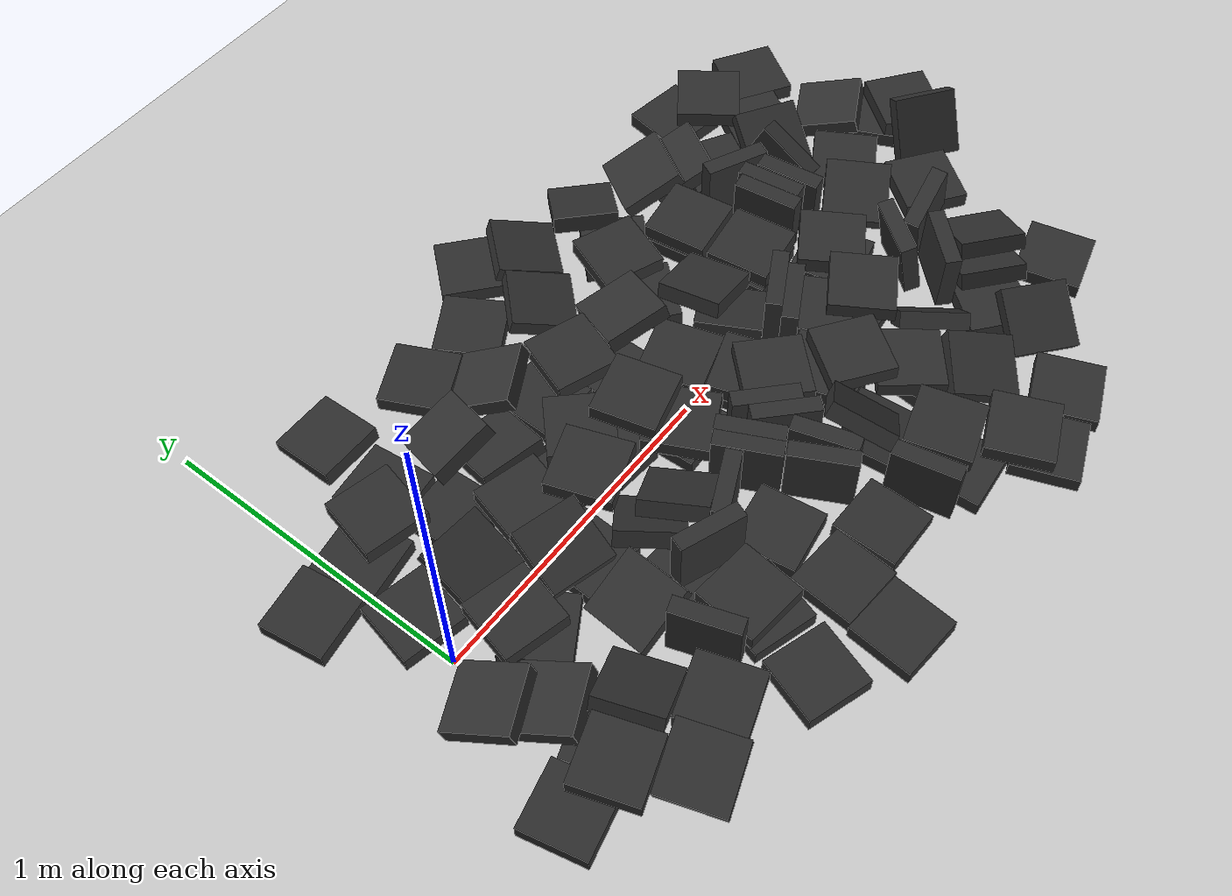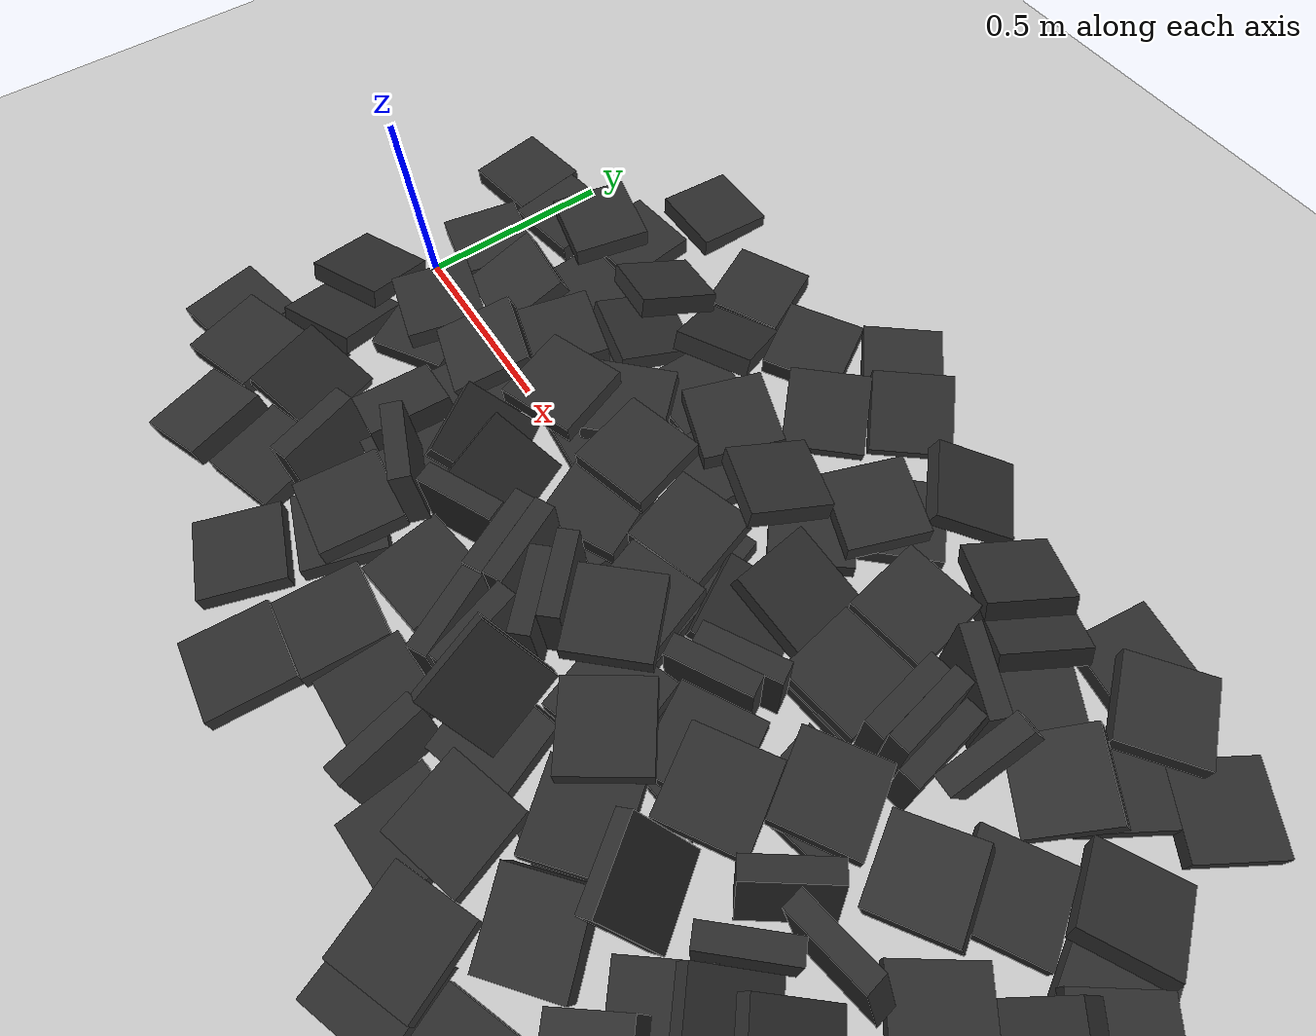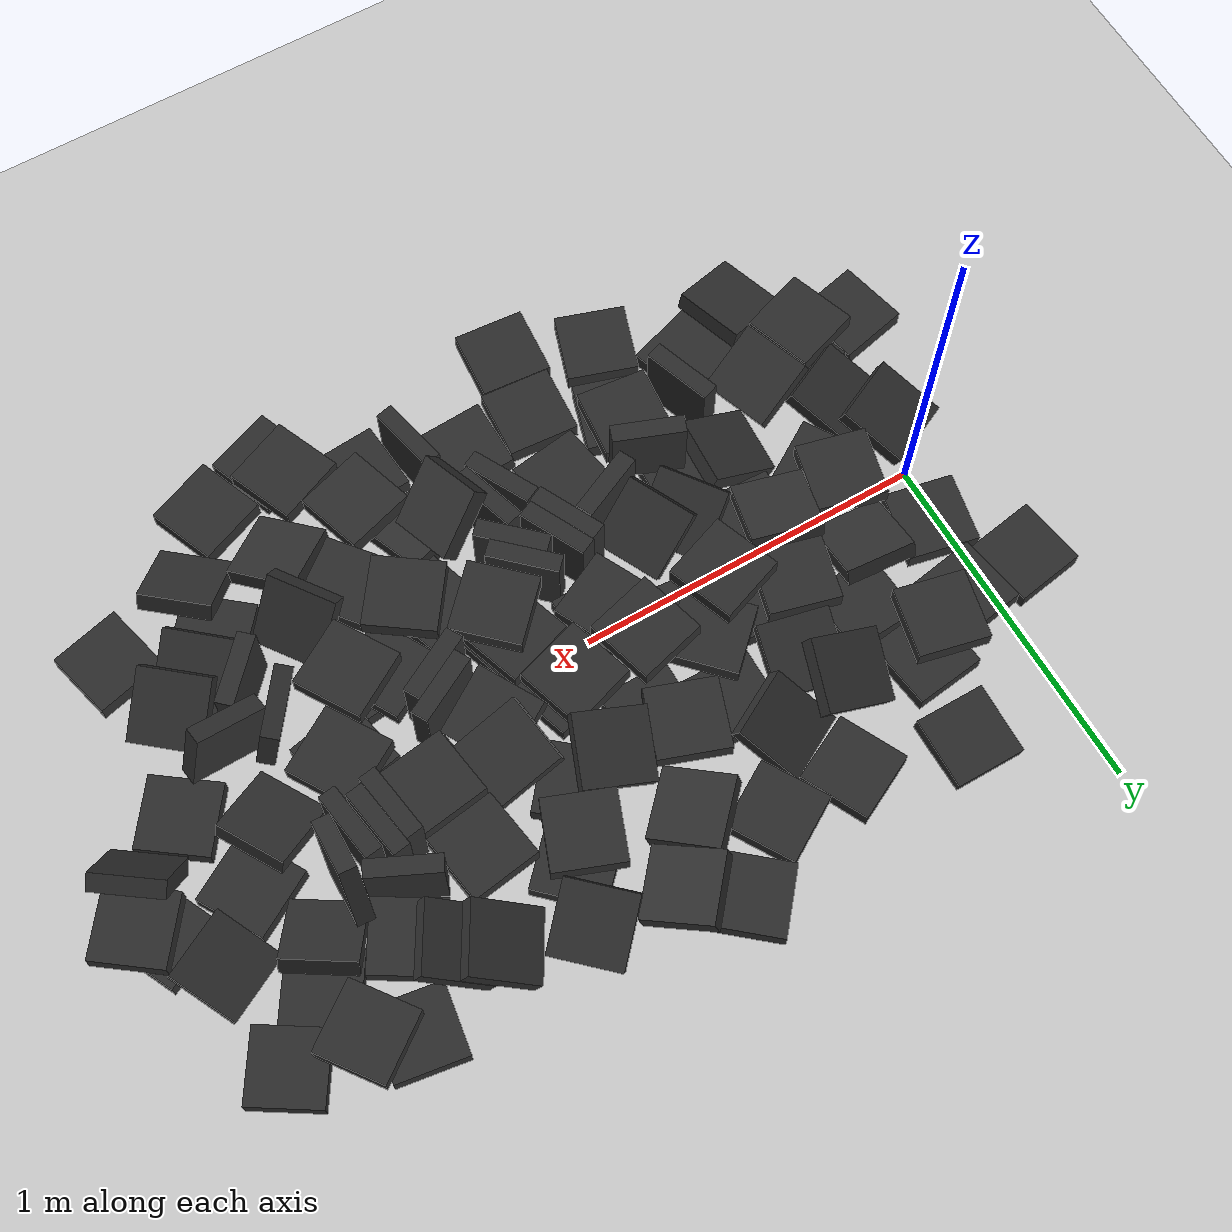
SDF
<sdf version="1.6">
 <world name="default">
  <light name="sun" type="directional">
   <pose>0 0 10 0 -0 0</pose>
   <diffuse>0.8 0.8 0.8 1</diffuse>
   <specular>0.1 0.1 0.1 1</specular>
   <attenuation>
    <range>1000</range>
    <constant>0.9</constant>
    <linear>0.01</linear>
    <quadratic>0.001</quadratic>
   </attenuation>
   <direction>-0.5 0.5 -1</direction>
  </light>
  <model name="ground_plane">
   <static>1</static>
   <link name="link">
    <collision name="collision">
     <geometry><plane><normal>0 0 1</normal><size>100 100</size></plane></geometry>
     <surface><friction><ode><mu>100</mu><mu2>50</mu2></ode></friction></surface>
    </collision>
    <visual name="visual">
     <cast_shadows>0</cast_shadows>
     <geometry><plane><normal>0 0 1</normal><size>100 100</size></plane></geometry>
     <material>
      <script><uri>file://media/materials/scripts/gazebo.material</uri><name>Gazebo/Grey</name></script>
     </material>
    </visual>
   </link>
  </model>
  <gravity>0 0 -9.8</gravity>
  <magnetic_field>6e-06 2.3e-05 -4.2e-05</magnetic_field>
  <atmosphere type="adiabatic"/>
  <physics name="default_physics" default="0" type="ode">
   <max_step_size>0.001</max_step_size>
   <real_time_factor>1</real_time_factor>
   <real_time_update_rate>1000</real_time_update_rate>
  </physics>
  <scene><ambient>0.4 0.4 0.4 1</ambient><background>0.7 0.7 0.7 1</background><shadows>1</shadows></scene>
  <spherical_coordinates>
   <surface_model>EARTH_WGS84</surface_model>
   <latitude_deg>0</latitude_deg>
   <longitude_deg>0</longitude_deg>
   <elevation>0</elevation>
   <heading_deg>0</heading_deg>
  </spherical_coordinates>
  <model name="gareki3">
   <static>1</static>
   <link name="BOX">
    <inertial>
     <mass>10</mass>
     <inertia><ixx>0.001</ixx><ixy>0</ixy><ixz>0</ixz><iyy>0.001</iyy><iyz>0</iyz><izz>0.001</izz></inertia>
    </inertial>
    <collision name="BOX_collision"><geometry><box><size>0.2 0.2 0.05</size></box></geometry></collision>
    <visual name="BOX_visual">
     <geometry><box><size>0.2 0.2 0.05</size></box></geometry>
     <material>
      <ambient>0.175 0.175 0.175 1.0</ambient>
      <diffuse>0.175 0.175 0.175 1.0</diffuse>
      <specular>0.175 0.175 0.175 1.0 1.5</specular>
     </material>
    </visual>
   </link>
   <pose>0.727338 0.072697 0.024895 -0.006319 0.000637 -0.089018</pose>
  </model>
  <model name="gareki0">
   <static>1</static>
   <link name="BOX">
    <inertial>
     <mass>10</mass>
     <inertia><ixx>0.001</ixx><ixy>0</ixy><ixz>0</ixz><iyy>0.001</iyy><iyz>0</iyz><izz>0.001</izz></inertia>
    </inertial>
    <collision name="BOX_collision"><geometry><box><size>0.2 0.2 0.05</size></box></geometry></collision>
    <visual name="BOX_visual">
     <geometry><box><size>0.2 0.2 0.05</size></box></geometry>
     <material>
      <ambient>0.175 0.175 0.175 1.0</ambient>
      <diffuse>0.175 0.175 0.175 1.0</diffuse>
      <specular>0.175 0.175 0.175 1.0 1.5</specular>
     </material>
    </visual>
   </link>
   <pose>0.526934 0.133943 0.024731 0.000444 0.008115 -0.155967</pose>
  </model>
  <model name="gareki1">
   <static>1</static>
   <link name="BOX">
    <inertial>
     <mass>10</mass>
     <inertia><ixx>0.001</ixx><ixy>0</ixy><ixz>0</ixz><iyy>0.001</iyy><iyz>0</iyz><izz>0.001</izz></inertia>
    </inertial>
    <collision name="BOX_collision"><geometry><box><size>0.2 0.2 0.05</size></box></geometry></collision>
    <visual name="BOX_visual">
     <geometry><box><size>0.2 0.2 0.05</size></box></geometry>
     <material>
      <ambient>0.175 0.175 0.175 1.0</ambient>
      <diffuse>0.175 0.175 0.175 1.0</diffuse>
      <specular>0.175 0.175 0.175 1.0 1.5</specular>
     </material>
    </visual>
   </link>
   <pose>0.07655 -0.448971 0.024951 0.001245 -0.000716 0.34208</pose>
  </model>
  <model name="gareki5">
   <static>1</static>
   <link name="BOX">
    <inertial>
     <mass>10</mass>
     <inertia><ixx>0.001</ixx><ixy>0</ixy><ixz>0</ixz><iyy>0.001</iyy><iyz>0</iyz><izz>0.001</izz></inertia>
    </inertial>
    <collision name="BOX_collision"><geometry><box><size>0.2 0.2 0.05</size></box></geometry></collision>
    <visual name="BOX_visual">
     <geometry><box><size>0.2 0.2 0.05</size></box></geometry>
     <material>
      <ambient>0.175 0.175 0.175 1.0</ambient>
      <diffuse>0.175 0.175 0.175 1.0</diffuse>
      <specular>0.175 0.175 0.175 1.0 1.5</specular>
     </material>
    </visual>
   </link>
   <pose>1.31628 -0.279888 0.024841 0.00025 -0.00043 0.307196</pose>
  </model>
  <model name="gareki4">
   <static>1</static>
   <link name="BOX">
    <inertial>
     <mass>10</mass>
     <inertia><ixx>0.001</ixx><ixy>0</ixy><ixz>0</ixz><iyy>0.001</iyy><iyz>0</iyz><izz>0.001</izz></inertia>
    </inertial>
    <collision name="BOX_collision"><geometry><box><size>0.2 0.2 0.05</size></box></geometry></collision>
    <visual name="BOX_visual">
     <geometry><box><size>0.2 0.2 0.05</size></box></geometry>
     <material>
      <ambient>0.175 0.175 0.175 1.0</ambient>
      <diffuse>0.175 0.175 0.175 1.0</diffuse>
      <specular>0.175 0.175 0.175 1.0 1.5</specular>
     </material>
    </visual>
   </link>
   <pose>0.324883 0.277416 0.024996 -0.003515 0.002962 -3.07923</pose>
  </model>
  <model name="gareki7">
   <static>1</static>
   <link name="BOX">
    <inertial>
     <mass>10</mass>
     <inertia><ixx>0.001</ixx><ixy>0</ixy><ixz>0</ixz><iyy>0.001</iyy><iyz>0</iyz><izz>0.001</izz></inertia>
    </inertial>
    <collision name="BOX_collision"><geometry><box><size>0.2 0.2 0.05</size></box></geometry></collision>
    <visual name="BOX_visual">
     <geometry><box><size>0.2 0.2 0.05</size></box></geometry>
     <material>
      <ambient>0.175 0.175 0.175 1.0</ambient>
      <diffuse>0.175 0.175 0.175 1.0</diffuse>
      <specular>0.175 0.175 0.175 1.0 1.5</specular>
     </material>
    </visual>
   </link>
   <pose>2.30266 0.175549 0.024939 0.003629 0.000413 0.447835</pose>
  </model>
  <model name="gareki8">
   <static>1</static>
   <link name="BOX">
    <inertial>
     <mass>10</mass>
     <inertia><ixx>0.001</ixx><ixy>0</ixy><ixz>0</ixz><iyy>0.001</iyy><iyz>0</iyz><izz>0.001</izz></inertia>
    </inertial>
    <collision name="BOX_collision"><geometry><box><size>0.2 0.2 0.05</size></box></geometry></collision>
    <visual name="BOX_visual">
     <geometry><box><size>0.2 0.2 0.05</size></box></geometry>
     <material>
      <ambient>0.175 0.175 0.175 1.0</ambient>
      <diffuse>0.175 0.175 0.175 1.0</diffuse>
      <specular>0.175 0.175 0.175 1.0 1.5</specular>
     </material>
    </visual>
   </link>
   <pose>1.51946 -0.190727 0.024965 0.000835 9.1e-05 0.103807</pose>
  </model>
  <model name="gareki10">
   <static>1</static>
   <link name="BOX">
    <inertial>
     <mass>10</mass>
     <inertia><ixx>0.001</ixx><ixy>0</ixy><ixz>0</ixz><iyy>0.001</iyy><iyz>0</iyz><izz>0.001</izz></inertia>
    </inertial>
    <collision name="BOX_collision"><geometry><box><size>0.2 0.2 0.05</size></box></geometry></collision>
    <visual name="BOX_visual">
     <geometry><box><size>0.2 0.2 0.05</size></box></geometry>
     <material>
      <ambient>0.175 0.175 0.175 1.0</ambient>
      <diffuse>0.175 0.175 0.175 1.0</diffuse>
      <specular>0.175 0.175 0.175 1.0 1.5</specular>
     </material>
    </visual>
   </link>
   <pose>1.51154 -0.460507 0.02488 -0.000364 0.000735 -0.093022</pose>
  </model>
  <model name="gareki12">
   <static>1</static>
   <link name="BOX">
    <inertial>
     <mass>10</mass>
     <inertia><ixx>0.001</ixx><ixy>0</ixy><ixz>0</ixz><iyy>0.001</iyy><iyz>0</iyz><izz>0.001</izz></inertia>
    </inertial>
    <collision name="BOX_collision"><geometry><box><size>0.2 0.2 0.05</size></box></geometry></collision>
    <visual name="BOX_visual">
     <geometry><box><size>0.2 0.2 0.05</size></box></geometry>
     <material>
      <ambient>0.175 0.175 0.175 1.0</ambient>
      <diffuse>0.175 0.175 0.175 1.0</diffuse>
      <specular>0.175 0.175 0.175 1.0 1.5</specular>
     </material>
    </visual>
   </link>
   <pose>0.028326 0.158663 0.025 -3.9e-05 -1.6e-05 -0.205768</pose>
  </model>
  <model name="gareki13">
   <static>1</static>
   <link name="BOX">
    <inertial>
     <mass>10</mass>
     <inertia><ixx>0.001</ixx><ixy>0</ixy><ixz>0</ixz><iyy>0.001</iyy><iyz>0</iyz><izz>0.001</izz></inertia>
    </inertial>
    <collision name="BOX_collision"><geometry><box><size>0.2 0.2 0.05</size></box></geometry></collision>
    <visual name="BOX_visual">
     <geometry><box><size>0.2 0.2 0.05</size></box></geometry>
     <material>
      <ambient>0.175 0.175 0.175 1.0</ambient>
      <diffuse>0.175 0.175 0.175 1.0</diffuse>
      <specular>0.175 0.175 0.175 1.0 1.5</specular>
     </material>
    </visual>
   </link>
   <pose>1.54433 0.165861 0.024951 0.000333 -0.000259 -1.45331</pose>
  </model>
  <model name="gareki2">
   <static>1</static>
   <link name="BOX">
    <inertial>
     <mass>10</mass>
     <inertia><ixx>0.001</ixx><ixy>0</ixy><ixz>0</ixz><iyy>0.001</iyy><iyz>0</iyz><izz>0.001</izz></inertia>
    </inertial>
    <collision name="BOX_collision"><geometry><box><size>0.2 0.2 0.05</size></box></geometry></collision>
    <visual name="BOX_visual">
     <geometry><box><size>0.2 0.2 0.05</size></box></geometry>
     <material>
      <ambient>0.175 0.175 0.175 1.0</ambient>
      <diffuse>0.175 0.175 0.175 1.0</diffuse>
      <specular>0.175 0.175 0.175 1.0 1.5</specular>
     </material>
    </visual>
   </link>
   <pose>0.543755 0.324039 0.051578 -0.27355 -0.005032 -0.220128</pose>
  </model>
  <model name="gareki15">
   <static>1</static>
   <link name="BOX">
    <inertial>
     <mass>10</mass>
     <inertia><ixx>0.001</ixx><ixy>0</ixy><ixz>0</ixz><iyy>0.001</iyy><iyz>0</iyz><izz>0.001</izz></inertia>
    </inertial>
    <collision name="BOX_collision"><geometry><box><size>0.2 0.2 0.05</size></box></geometry></collision>
    <visual name="BOX_visual">
     <geometry><box><size>0.2 0.2 0.05</size></box></geometry>
     <material>
      <ambient>0.175 0.175 0.175 1.0</ambient>
      <diffuse>0.175 0.175 0.175 1.0</diffuse>
      <specular>0.175 0.175 0.175 1.0 1.5</specular>
     </material>
    </visual>
   </link>
   <pose>0.288718 0.729996 0.016046 -0.092922 0 0</pose>
  </model>
  <model name="gareki16">
   <static>1</static>
   <link name="BOX">
    <inertial>
     <mass>10</mass>
     <inertia><ixx>0.001</ixx><ixy>0</ixy><ixz>0</ixz><iyy>0.001</iyy><iyz>0</iyz><izz>0.001</izz></inertia>
    </inertial>
    <collision name="BOX_collision"><geometry><box><size>0.2 0.2 0.05</size></box></geometry></collision>
    <visual name="BOX_visual">
     <geometry><box><size>0.2 0.2 0.05</size></box></geometry>
     <material>
      <ambient>0.175 0.175 0.175 1.0</ambient>
      <diffuse>0.175 0.175 0.175 1.0</diffuse>
      <specular>0.175 0.175 0.175 1.0 1.5</specular>
     </material>
    </visual>
   </link>
   <pose>1.84904 -0.501389 0.024959 0.000278 -2.6e-05 -0.69052</pose>
  </model>
  <model name="gareki6">
   <static>1</static>
   <link name="BOX">
    <inertial>
     <mass>10</mass>
     <inertia><ixx>0.001</ixx><ixy>0</ixy><ixz>0</ixz><iyy>0.001</iyy><iyz>0</iyz><izz>0.001</izz></inertia>
    </inertial>
    <collision name="BOX_collision"><geometry><box><size>0.2 0.2 0.05</size></box></geometry></collision>
    <visual name="BOX_visual">
     <geometry><box><size>0.2 0.2 0.05</size></box></geometry>
     <material>
      <ambient>0.175 0.175 0.175 1.0</ambient>
      <diffuse>0.175 0.175 0.175 1.0</diffuse>
      <specular>0.175 0.175 0.175 1.0 1.5</specular>
     </material>
    </visual>
   </link>
   <pose>0.93069 -0.037854 0.024959 0.000599 -0.000422 0.044697</pose>
  </model>
  <model name="gareki9">
   <static>1</static>
   <link name="BOX">
    <inertial>
     <mass>10</mass>
     <inertia><ixx>0.001</ixx><ixy>0</ixy><ixz>0</ixz><iyy>0.001</iyy><iyz>0</iyz><izz>0.001</izz></inertia>
    </inertial>
    <collision name="BOX_collision"><geometry><box><size>0.2 0.2 0.05</size></box></geometry></collision>
    <visual name="BOX_visual">
     <geometry><box><size>0.2 0.2 0.05</size></box></geometry>
     <material>
      <ambient>0.175 0.175 0.175 1.0</ambient>
      <diffuse>0.175 0.175 0.175 1.0</diffuse>
      <specular>0.175 0.175 0.175 1.0 1.5</specular>
     </material>
    </visual>
   </link>
   <pose>1.78897 0.477938 0.024999 -0.000143 -0.000227 1.03353</pose>
  </model>
  <model name="gareki11">
   <static>1</static>
   <link name="BOX">
    <inertial>
     <mass>10</mass>
     <inertia><ixx>0.001</ixx><ixy>0</ixy><ixz>0</ixz><iyy>0.001</iyy><iyz>0</iyz><izz>0.001</izz></inertia>
    </inertial>
    <collision name="BOX_collision"><geometry><box><size>0.2 0.2 0.05</size></box></geometry></collision>
    <visual name="BOX_visual">
     <geometry><box><size>0.2 0.2 0.05</size></box></geometry>
     <material>
      <ambient>0.175 0.175 0.175 1.0</ambient>
      <diffuse>0.175 0.175 0.175 1.0</diffuse>
      <specular>0.175 0.175 0.175 1.0 1.5</specular>
     </material>
    </visual>
   </link>
   <pose>1.22892 0.336084 0.02473 4.4e-05 -0.002733 0.872295</pose>
  </model>
  <model name="gareki17">
   <static>1</static>
   <link name="BOX">
    <inertial>
     <mass>10</mass>
     <inertia><ixx>0.001</ixx><ixy>0</ixy><ixz>0</ixz><iyy>0.001</iyy><iyz>0</iyz><izz>0.001</izz></inertia>
    </inertial>
    <collision name="BOX_collision"><geometry><box><size>0.2 0.2 0.05</size></box></geometry></collision>
    <visual name="BOX_visual">
     <geometry><box><size>0.2 0.2 0.05</size></box></geometry>
     <material>
      <ambient>0.175 0.175 0.175 1.0</ambient>
      <diffuse>0.175 0.175 0.175 1.0</diffuse>
      <specular>0.175 0.175 0.175 1.0 1.5</specular>
     </material>
    </visual>
   </link>
   <pose>1.06244 -0.222001 0.100002 1.57085 -1e-06 -0.761516</pose>
  </model>
  <model name="gareki18">
   <static>1</static>
   <link name="BOX">
    <inertial>
     <mass>10</mass>
     <inertia><ixx>0.001</ixx><ixy>0</ixy><ixz>0</ixz><iyy>0.001</iyy><iyz>0</iyz><izz>0.001</izz></inertia>
    </inertial>
    <collision name="BOX_collision"><geometry><box><size>0.2 0.2 0.05</size></box></geometry></collision>
    <visual name="BOX_visual">
     <geometry><box><size>0.2 0.2 0.05</size></box></geometry>
     <material>
      <ambient>0.175 0.175 0.175 1.0</ambient>
      <diffuse>0.175 0.175 0.175 1.0</diffuse>
      <specular>0.175 0.175 0.175 1.0 1.5</specular>
     </material>
    </visual>
   </link>
   <pose>1.01081 -0.655456 0.016063 -1.1e-05 0.092734 0.001786</pose>
  </model>
  <model name="gareki21">
   <static>1</static>
   <link name="BOX">
    <inertial>
     <mass>10</mass>
     <inertia><ixx>0.001</ixx><ixy>0</ixy><ixz>0</ixz><iyy>0.001</iyy><iyz>0</iyz><izz>0.001</izz></inertia>
    </inertial>
    <collision name="BOX_collision"><geometry><box><size>0.2 0.2 0.05</size></box></geometry></collision>
    <visual name="BOX_visual">
     <geometry><box><size>0.2 0.2 0.05</size></box></geometry>
     <material>
      <ambient>0.175 0.175 0.175 1.0</ambient>
      <diffuse>0.175 0.175 0.175 1.0</diffuse>
      <specular>0.175 0.175 0.175 1.0 1.5</specular>
     </material>
    </visual>
   </link>
   <pose>1.93168 -0.414184 0.067992 -0.466734 -0.006939 -0.706662</pose>
  </model>
  <model name="gareki14">
   <static>1</static>
   <link name="BOX">
    <inertial>
     <mass>10</mass>
     <inertia><ixx>0.001</ixx><ixy>0</ixy><ixz>0</ixz><iyy>0.001</iyy><iyz>0</iyz><izz>0.001</izz></inertia>
    </inertial>
    <collision name="BOX_collision"><geometry><box><size>0.2 0.2 0.05</size></box></geometry></collision>
    <visual name="BOX_visual">
     <geometry><box><size>0.2 0.2 0.05</size></box></geometry>
     <material>
      <ambient>0.175 0.175 0.175 1.0</ambient>
      <diffuse>0.175 0.175 0.175 1.0</diffuse>
      <specular>0.175 0.175 0.175 1.0 1.5</specular>
     </material>
    </visual>
   </link>
   <pose>0.533327 -0.32418 0.024981 1.6e-05 2.9e-05 -1.63397</pose>
  </model>
  <model name="gareki28">
   <static>1</static>
   <link name="BOX">
    <inertial>
     <mass>10</mass>
     <inertia><ixx>0.001</ixx><ixy>0</ixy><ixz>0</ixz><iyy>0.001</iyy><iyz>0</iyz><izz>0.001</izz></inertia>
    </inertial>
    <collision name="BOX_collision"><geometry><box><size>0.2 0.2 0.05</size></box></geometry></collision>
    <visual name="BOX_visual">
     <geometry><box><size>0.2 0.2 0.05</size></box></geometry>
     <material>
      <ambient>0.175 0.175 0.175 1.0</ambient>
      <diffuse>0.175 0.175 0.175 1.0</diffuse>
      <specular>0.175 0.175 0.175 1.0 1.5</specular>
     </material>
    </visual>
   </link>
   <pose>1.06061 -0.289358 0.099992 1.57087 2.1e-05 -0.761632</pose>
  </model>
  <model name="gareki27">
   <static>1</static>
   <link name="BOX">
    <inertial>
     <mass>10</mass>
     <inertia><ixx>0.001</ixx><ixy>0</ixy><ixz>0</ixz><iyy>0.001</iyy><iyz>0</iyz><izz>0.001</izz></inertia>
    </inertial>
    <collision name="BOX_collision"><geometry><box><size>0.2 0.2 0.05</size></box></geometry></collision>
    <visual name="BOX_visual">
     <geometry><box><size>0.2 0.2 0.05</size></box></geometry>
     <material>
      <ambient>0.175 0.175 0.175 1.0</ambient>
      <diffuse>0.175 0.175 0.175 1.0</diffuse>
      <specular>0.175 0.175 0.175 1.0 1.5</specular>
     </material>
    </visual>
   </link>
   <pose>0.260534 0.484094 0.024989 -0.000544 -0.000708 0.120012</pose>
  </model>
  <model name="gareki23">
   <static>1</static>
   <link name="BOX">
    <inertial>
     <mass>10</mass>
     <inertia><ixx>0.001</ixx><ixy>0</ixy><ixz>0</ixz><iyy>0.001</iyy><iyz>0</iyz><izz>0.001</izz></inertia>
    </inertial>
    <collision name="BOX_collision"><geometry><box><size>0.2 0.2 0.05</size></box></geometry></collision>
    <visual name="BOX_visual">
     <geometry><box><size>0.2 0.2 0.05</size></box></geometry>
     <material>
      <ambient>0.175 0.175 0.175 1.0</ambient>
      <diffuse>0.175 0.175 0.175 1.0</diffuse>
      <specular>0.175 0.175 0.175 1.0 1.5</specular>
     </material>
    </visual>
   </link>
   <pose>1.29793 -0.730407 0.02499 0.000827 0.000759 0.078773</pose>
  </model>
  <model name="gareki24">
   <static>1</static>
   <link name="BOX">
    <inertial>
     <mass>10</mass>
     <inertia><ixx>0.001</ixx><ixy>0</ixy><ixz>0</ixz><iyy>0.001</iyy><iyz>0</iyz><izz>0.001</izz></inertia>
    </inertial>
    <collision name="BOX_collision"><geometry><box><size>0.2 0.2 0.05</size></box></geometry></collision>
    <visual name="BOX_visual">
     <geometry><box><size>0.2 0.2 0.05</size></box></geometry>
     <material>
      <ambient>0.175 0.175 0.175 1.0</ambient>
      <diffuse>0.175 0.175 0.175 1.0</diffuse>
      <specular>0.175 0.175 0.175 1.0 1.5</specular>
     </material>
    </visual>
   </link>
   <pose>0.763953 0.335618 0.024998 -0.000655 3.7e-05 -0.0041</pose>
  </model>
  <model name="gareki26">
   <static>1</static>
   <link name="BOX">
    <inertial>
     <mass>10</mass>
     <inertia><ixx>0.001</ixx><ixy>0</ixy><ixz>0</ixz><iyy>0.001</iyy><iyz>0</iyz><izz>0.001</izz></inertia>
    </inertial>
    <collision name="BOX_collision"><geometry><box><size>0.2 0.2 0.05</size></box></geometry></collision>
    <visual name="BOX_visual">
     <geometry><box><size>0.2 0.2 0.05</size></box></geometry>
     <material>
      <ambient>0.175 0.175 0.175 1.0</ambient>
      <diffuse>0.175 0.175 0.175 1.0</diffuse>
      <specular>0.175 0.175 0.175 1.0 1.5</specular>
     </material>
    </visual>
   </link>
   <pose>0.949059 -0.250492 0.099986 1.57089 -0.000319 -1.11763</pose>
  </model>
  <model name="gareki22">
   <static>1</static>
   <link name="BOX">
    <inertial>
     <mass>10</mass>
     <inertia><ixx>0.001</ixx><ixy>0</ixy><ixz>0</ixz><iyy>0.001</iyy><iyz>0</iyz><izz>0.001</izz></inertia>
    </inertial>
    <collision name="BOX_collision"><geometry><box><size>0.2 0.2 0.05</size></box></geometry></collision>
    <visual name="BOX_visual">
     <geometry><box><size>0.2 0.2 0.05</size></box></geometry>
     <material>
      <ambient>0.175 0.175 0.175 1.0</ambient>
      <diffuse>0.175 0.175 0.175 1.0</diffuse>
      <specular>0.175 0.175 0.175 1.0 1.5</specular>
     </material>
    </visual>
   </link>
   <pose>1.01077 0.551392 0.051467 -0.277361 0.000777 -2.331</pose>
  </model>
  <model name="gareki29">
   <static>1</static>
   <link name="BOX">
    <inertial>
     <mass>10</mass>
     <inertia><ixx>0.001</ixx><ixy>0</ixy><ixz>0</ixz><iyy>0.001</iyy><iyz>0</iyz><izz>0.001</izz></inertia>
    </inertial>
    <collision name="BOX_collision"><geometry><box><size>0.2 0.2 0.05</size></box></geometry></collision>
    <visual name="BOX_visual">
     <geometry><box><size>0.2 0.2 0.05</size></box></geometry>
     <material>
      <ambient>0.175 0.175 0.175 1.0</ambient>
      <diffuse>0.175 0.175 0.175 1.0</diffuse>
      <specular>0.175 0.175 0.175 1.0 1.5</specular>
     </material>
    </visual>
   </link>
   <pose>2.03289 -0.351604 0.067237 -0.465417 -0.000509 -0.69697</pose>
  </model>
  <model name="gareki20">
   <static>1</static>
   <link name="BOX">
    <inertial>
     <mass>10</mass>
     <inertia><ixx>0.001</ixx><ixy>0</ixy><ixz>0</ixz><iyy>0.001</iyy><iyz>0</iyz><izz>0.001</izz></inertia>
    </inertial>
    <collision name="BOX_collision"><geometry><box><size>0.2 0.2 0.05</size></box></geometry></collision>
    <visual name="BOX_visual">
     <geometry><box><size>0.2 0.2 0.05</size></box></geometry>
     <material>
      <ambient>0.175 0.175 0.175 1.0</ambient>
      <diffuse>0.175 0.175 0.175 1.0</diffuse>
      <specular>0.175 0.175 0.175 1.0 1.5</specular>
     </material>
    </visual>
   </link>
   <pose>1.3323 0.519286 0.024993 3.5e-05 -1.1e-05 -0.767742</pose>
  </model>
  <model name="gareki31">
   <static>1</static>
   <link name="BOX">
    <inertial>
     <mass>10</mass>
     <inertia><ixx>0.001</ixx><ixy>0</ixy><ixz>0</ixz><iyy>0.001</iyy><iyz>0</iyz><izz>0.001</izz></inertia>
    </inertial>
    <collision name="BOX_collision"><geometry><box><size>0.2 0.2 0.05</size></box></geometry></collision>
    <visual name="BOX_visual">
     <geometry><box><size>0.2 0.2 0.05</size></box></geometry>
     <material>
      <ambient>0.175 0.175 0.175 1.0</ambient>
      <diffuse>0.175 0.175 0.175 1.0</diffuse>
      <specular>0.175 0.175 0.175 1.0 1.5</specular>
     </material>
    </visual>
   </link>
   <pose>1.51936 0.366992 0.024972 -0.000237 -5e-06 -1.4264</pose>
  </model>
  <model name="gareki33">
   <static>1</static>
   <link name="BOX">
    <inertial>
     <mass>10</mass>
     <inertia><ixx>0.001</ixx><ixy>0</ixy><ixz>0</ixz><iyy>0.001</iyy><iyz>0</iyz><izz>0.001</izz></inertia>
    </inertial>
    <collision name="BOX_collision"><geometry><box><size>0.2 0.2 0.05</size></box></geometry></collision>
    <visual name="BOX_visual">
     <geometry><box><size>0.2 0.2 0.05</size></box></geometry>
     <material>
      <ambient>0.175 0.175 0.175 1.0</ambient>
      <diffuse>0.175 0.175 0.175 1.0</diffuse>
      <specular>0.175 0.175 0.175 1.0 1.5</specular>
     </material>
    </visual>
   </link>
   <pose>1.50092 -0.892813 0.024793 -0.00125 0.001185 0.365437</pose>
  </model>
  <model name="gareki37">
   <static>1</static>
   <link name="BOX">
    <inertial>
     <mass>10</mass>
     <inertia><ixx>0.001</ixx><ixy>0</ixy><ixz>0</ixz><iyy>0.001</iyy><iyz>0</iyz><izz>0.001</izz></inertia>
    </inertial>
    <collision name="BOX_collision"><geometry><box><size>0.2 0.2 0.05</size></box></geometry></collision>
    <visual name="BOX_visual">
     <geometry><box><size>0.2 0.2 0.05</size></box></geometry>
     <material>
      <ambient>0.175 0.175 0.175 1.0</ambient>
      <diffuse>0.175 0.175 0.175 1.0</diffuse>
      <specular>0.175 0.175 0.175 1.0 1.5</specular>
     </material>
    </visual>
   </link>
   <pose>1.18254 -0.112425 0.024887 -0.000933 4.2e-05 0.308765</pose>
  </model>
  <model name="gareki32">
   <static>1</static>
   <link name="BOX">
    <inertial>
     <mass>10</mass>
     <inertia><ixx>0.001</ixx><ixy>0</ixy><ixz>0</ixz><iyy>0.001</iyy><iyz>0</iyz><izz>0.001</izz></inertia>
    </inertial>
    <collision name="BOX_collision"><geometry><box><size>0.2 0.2 0.05</size></box></geometry></collision>
    <visual name="BOX_visual">
     <geometry><box><size>0.2 0.2 0.05</size></box></geometry>
     <material>
      <ambient>0.175 0.175 0.175 1.0</ambient>
      <diffuse>0.175 0.175 0.175 1.0</diffuse>
      <specular>0.175 0.175 0.175 1.0 1.5</specular>
     </material>
    </visual>
   </link>
   <pose>1.55369 0.169864 0.074943 3.4e-05 -7.5e-05 -1.42645</pose>
  </model>
  <model name="gareki19">
   <static>1</static>
   <link name="BOX">
    <inertial>
     <mass>10</mass>
     <inertia><ixx>0.001</ixx><ixy>0</ixy><ixz>0</ixz><iyy>0.001</iyy><iyz>0</iyz><izz>0.001</izz></inertia>
    </inertial>
    <collision name="BOX_collision"><geometry><box><size>0.2 0.2 0.05</size></box></geometry></collision>
    <visual name="BOX_visual">
     <geometry><box><size>0.2 0.2 0.05</size></box></geometry>
     <material>
      <ambient>0.175 0.175 0.175 1.0</ambient>
      <diffuse>0.175 0.175 0.175 1.0</diffuse>
      <specular>0.175 0.175 0.175 1.0 1.5</specular>
     </material>
    </visual>
   </link>
   <pose>1.15485 -0.685166 0.100098 1.56819 0.000911 -1.36102</pose>
  </model>
  <model name="gareki36">
   <static>1</static>
   <link name="BOX">
    <inertial>
     <mass>10</mass>
     <inertia><ixx>0.001</ixx><ixy>0</ixy><ixz>0</ixz><iyy>0.001</iyy><iyz>0</iyz><izz>0.001</izz></inertia>
    </inertial>
    <collision name="BOX_collision"><geometry><box><size>0.2 0.2 0.05</size></box></geometry></collision>
    <visual name="BOX_visual">
     <geometry><box><size>0.2 0.2 0.05</size></box></geometry>
     <material>
      <ambient>0.175 0.175 0.175 1.0</ambient>
      <diffuse>0.175 0.175 0.175 1.0</diffuse>
      <specular>0.175 0.175 0.175 1.0 1.5</specular>
     </material>
    </visual>
   </link>
   <pose>0.776019 -0.866008 0.024998 2e-05 -1.8e-05 -0.083468</pose>
  </model>
  <model name="gareki34">
   <static>1</static>
   <link name="BOX">
    <inertial>
     <mass>10</mass>
     <inertia><ixx>0.001</ixx><ixy>0</ixy><ixz>0</ixz><iyy>0.001</iyy><iyz>0</iyz><izz>0.001</izz></inertia>
    </inertial>
    <collision name="BOX_collision"><geometry><box><size>0.2 0.2 0.05</size></box></geometry></collision>
    <visual name="BOX_visual">
     <geometry><box><size>0.2 0.2 0.05</size></box></geometry>
     <material>
      <ambient>0.175 0.175 0.175 1.0</ambient>
      <diffuse>0.175 0.175 0.175 1.0</diffuse>
      <specular>0.175 0.175 0.175 1.0 1.5</specular>
     </material>
    </visual>
   </link>
   <pose>1.70189 -0.029203 0.024994 -0.001191 0.001314 0.20836</pose>
  </model>
  <model name="gareki35">
   <static>1</static>
   <link name="BOX">
    <inertial>
     <mass>10</mass>
     <inertia><ixx>0.001</ixx><ixy>0</ixy><ixz>0</ixz><iyy>0.001</iyy><iyz>0</iyz><izz>0.001</izz></inertia>
    </inertial>
    <collision name="BOX_collision"><geometry><box><size>0.2 0.2 0.05</size></box></geometry></collision>
    <visual name="BOX_visual">
     <geometry><box><size>0.2 0.2 0.05</size></box></geometry>
     <material>
      <ambient>0.175 0.175 0.175 1.0</ambient>
      <diffuse>0.175 0.175 0.175 1.0</diffuse>
      <specular>0.175 0.175 0.175 1.0 1.5</specular>
     </material>
    </visual>
   </link>
   <pose>0.826051 0.659003 0.024996 0.00046 0.000318 0.536156</pose>
  </model>
  <model name="gareki39">
   <static>1</static>
   <link name="BOX">
    <inertial>
     <mass>10</mass>
     <inertia><ixx>0.001</ixx><ixy>0</ixy><ixz>0</ixz><iyy>0.001</iyy><iyz>0</iyz><izz>0.001</izz></inertia>
    </inertial>
    <collision name="BOX_collision"><geometry><box><size>0.2 0.2 0.05</size></box></geometry></collision>
    <visual name="BOX_visual">
     <geometry><box><size>0.2 0.2 0.05</size></box></geometry>
     <material>
      <ambient>0.175 0.175 0.175 1.0</ambient>
      <diffuse>0.175 0.175 0.175 1.0</diffuse>
      <specular>0.175 0.175 0.175 1.0 1.5</specular>
     </material>
    </visual>
   </link>
   <pose>1.87757 0.702094 0.024663 0.003381 -1.9e-05 -0.154785</pose>
  </model>
  <model name="gareki41">
   <static>1</static>
   <link name="BOX">
    <inertial>
     <mass>10</mass>
     <inertia><ixx>0.001</ixx><ixy>0</ixy><ixz>0</ixz><iyy>0.001</iyy><iyz>0</iyz><izz>0.001</izz></inertia>
    </inertial>
    <collision name="BOX_collision"><geometry><box><size>0.2 0.2 0.05</size></box></geometry></collision>
    <visual name="BOX_visual">
     <geometry><box><size>0.2 0.2 0.05</size></box></geometry>
     <material>
      <ambient>0.175 0.175 0.175 1.0</ambient>
      <diffuse>0.175 0.175 0.175 1.0</diffuse>
      <specular>0.175 0.175 0.175 1.0 1.5</specular>
     </material>
    </visual>
   </link>
   <pose>2.19023 0.618485 0.024997 -2.4e-05 -1.2e-05 1.00492</pose>
  </model>
  <model name="gareki25">
   <static>1</static>
   <link name="BOX">
    <inertial>
     <mass>10</mass>
     <inertia><ixx>0.001</ixx><ixy>0</ixy><ixz>0</ixz><iyy>0.001</iyy><iyz>0</iyz><izz>0.001</izz></inertia>
    </inertial>
    <collision name="BOX_collision"><geometry><box><size>0.2 0.2 0.05</size></box></geometry></collision>
    <visual name="BOX_visual">
     <geometry><box><size>0.2 0.2 0.05</size></box></geometry>
     <material>
      <ambient>0.175 0.175 0.175 1.0</ambient>
      <diffuse>0.175 0.175 0.175 1.0</diffuse>
      <specular>0.175 0.175 0.175 1.0 1.5</specular>
     </material>
    </visual>
   </link>
   <pose>0.99652 0.812877 0.024986 -7.8e-05 0.000308 2.43506</pose>
  </model>
  <model name="gareki38">
   <static>1</static>
   <link name="BOX">
    <inertial>
     <mass>10</mass>
     <inertia><ixx>0.001</ixx><ixy>0</ixy><ixz>0</ixz><iyy>0.001</iyy><iyz>0</iyz><izz>0.001</izz></inertia>
    </inertial>
    <collision name="BOX_collision"><geometry><box><size>0.2 0.2 0.05</size></box></geometry></collision>
    <visual name="BOX_visual">
     <geometry><box><size>0.2 0.2 0.05</size></box></geometry>
     <material>
      <ambient>0.175 0.175 0.175 1.0</ambient>
      <diffuse>0.175 0.175 0.175 1.0</diffuse>
      <specular>0.175 0.175 0.175 1.0 1.5</specular>
     </material>
    </visual>
   </link>
   <pose>0.332723 -0.608174 0.024992 0.001324 0.000771 0.320978</pose>
  </model>
  <model name="gareki42">
   <static>1</static>
   <link name="BOX">
    <inertial>
     <mass>10</mass>
     <inertia><ixx>0.001</ixx><ixy>0</ixy><ixz>0</ixz><iyy>0.001</iyy><iyz>0</iyz><izz>0.001</izz></inertia>
    </inertial>
    <collision name="BOX_collision"><geometry><box><size>0.2 0.2 0.05</size></box></geometry></collision>
    <visual name="BOX_visual">
     <geometry><box><size>0.2 0.2 0.05</size></box></geometry>
     <material>
      <ambient>0.175 0.175 0.175 1.0</ambient>
      <diffuse>0.175 0.175 0.175 1.0</diffuse>
      <specular>0.175 0.175 0.175 1.0 1.5</specular>
     </material>
    </visual>
   </link>
   <pose>0.917537 -0.043055 0.074792 0.010577 0.011705 2.02669</pose>
  </model>
  <model name="gareki43">
   <static>1</static>
   <link name="BOX">
    <inertial>
     <mass>10</mass>
     <inertia><ixx>0.001</ixx><ixy>0</ixy><ixz>0</ixz><iyy>0.001</iyy><iyz>0</iyz><izz>0.001</izz></inertia>
    </inertial>
    <collision name="BOX_collision"><geometry><box><size>0.2 0.2 0.05</size></box></geometry></collision>
    <visual name="BOX_visual">
     <geometry><box><size>0.2 0.2 0.05</size></box></geometry>
     <material>
      <ambient>0.175 0.175 0.175 1.0</ambient>
      <diffuse>0.175 0.175 0.175 1.0</diffuse>
      <specular>0.175 0.175 0.175 1.0 1.5</specular>
     </material>
    </visual>
   </link>
   <pose>1.32569 0.080378 0.053458 2.84528 0.005474 -1.07289</pose>
  </model>
  <model name="gareki48">
   <static>1</static>
   <link name="BOX">
    <inertial>
     <mass>10</mass>
     <inertia><ixx>0.001</ixx><ixy>0</ixy><ixz>0</ixz><iyy>0.001</iyy><iyz>0</iyz><izz>0.001</izz></inertia>
    </inertial>
    <collision name="BOX_collision"><geometry><box><size>0.2 0.2 0.05</size></box></geometry></collision>
    <visual name="BOX_visual">
     <geometry><box><size>0.2 0.2 0.05</size></box></geometry>
     <material>
      <ambient>0.175 0.175 0.175 1.0</ambient>
      <diffuse>0.175 0.175 0.175 1.0</diffuse>
      <specular>0.175 0.175 0.175 1.0 1.5</specular>
     </material>
    </visual>
   </link>
   <pose>1.70489 -0.836145 0.024947 0.000112 0.000276 0.380636</pose>
  </model>
  <model name="gareki49">
   <static>1</static>
   <link name="BOX">
    <inertial>
     <mass>10</mass>
     <inertia><ixx>0.001</ixx><ixy>0</ixy><ixz>0</ixz><iyy>0.001</iyy><iyz>0</iyz><izz>0.001</izz></inertia>
    </inertial>
    <collision name="BOX_collision"><geometry><box><size>0.2 0.2 0.05</size></box></geometry></collision>
    <visual name="BOX_visual">
     <geometry><box><size>0.2 0.2 0.05</size></box></geometry>
     <material>
      <ambient>0.175 0.175 0.175 1.0</ambient>
      <diffuse>0.175 0.175 0.175 1.0</diffuse>
      <specular>0.175 0.175 0.175 1.0 1.5</specular>
     </material>
    </visual>
   </link>
   <pose>1.42078 -0.010259 0.100002 -1.57085 0.000117 -2.64271</pose>
  </model>
  <model name="gareki30">
   <static>1</static>
   <link name="BOX">
    <inertial>
     <mass>10</mass>
     <inertia><ixx>0.001</ixx><ixy>0</ixy><ixz>0</ixz><iyy>0.001</iyy><iyz>0</iyz><izz>0.001</izz></inertia>
    </inertial>
    <collision name="BOX_collision"><geometry><box><size>0.2 0.2 0.05</size></box></geometry></collision>
    <visual name="BOX_visual">
     <geometry><box><size>0.2 0.2 0.05</size></box></geometry>
     <material>
      <ambient>0.175 0.175 0.175 1.0</ambient>
      <diffuse>0.175 0.175 0.175 1.0</diffuse>
      <specular>0.175 0.175 0.175 1.0 1.5</specular>
     </material>
    </visual>
   </link>
   <pose>1.06034 -0.421717 0.099999 1.57073 0.000328 -1.27472</pose>
  </model>
  <model name="gareki40">
   <static>1</static>
   <link name="BOX">
    <inertial>
     <mass>10</mass>
     <inertia><ixx>0.001</ixx><ixy>0</ixy><ixz>0</ixz><iyy>0.001</iyy><iyz>0</iyz><izz>0.001</izz></inertia>
    </inertial>
    <collision name="BOX_collision"><geometry><box><size>0.2 0.2 0.05</size></box></geometry></collision>
    <visual name="BOX_visual">
     <geometry><box><size>0.2 0.2 0.05</size></box></geometry>
     <material>
      <ambient>0.175 0.175 0.175 1.0</ambient>
      <diffuse>0.175 0.175 0.175 1.0</diffuse>
      <specular>0.175 0.175 0.175 1.0 1.5</specular>
     </material>
    </visual>
   </link>
   <pose>1.69483 0.559943 0.066556 -0.457202 -0.000157 1.03537</pose>
  </model>
  <model name="gareki45">
   <static>1</static>
   <link name="BOX">
    <inertial>
     <mass>10</mass>
     <inertia><ixx>0.001</ixx><ixy>0</ixy><ixz>0</ixz><iyy>0.001</iyy><iyz>0</iyz><izz>0.001</izz></inertia>
    </inertial>
    <collision name="BOX_collision"><geometry><box><size>0.2 0.2 0.05</size></box></geometry></collision>
    <visual name="BOX_visual">
     <geometry><box><size>0.2 0.2 0.05</size></box></geometry>
     <material>
      <ambient>0.175 0.175 0.175 1.0</ambient>
      <diffuse>0.175 0.175 0.175 1.0</diffuse>
      <specular>0.175 0.175 0.175 1.0 1.5</specular>
     </material>
    </visual>
   </link>
   <pose>2.11806 -0.565214 0.024998 -1.7e-05 -1.9e-05 -1.32703</pose>
  </model>
  <model name="gareki53">
   <static>1</static>
   <link name="BOX">
    <inertial>
     <mass>10</mass>
     <inertia><ixx>0.001</ixx><ixy>0</ixy><ixz>0</ixz><iyy>0.001</iyy><iyz>0</iyz><izz>0.001</izz></inertia>
    </inertial>
    <collision name="BOX_collision"><geometry><box><size>0.2 0.2 0.05</size></box></geometry></collision>
    <visual name="BOX_visual">
     <geometry><box><size>0.2 0.2 0.05</size></box></geometry>
     <material>
      <ambient>0.175 0.175 0.175 1.0</ambient>
      <diffuse>0.175 0.175 0.175 1.0</diffuse>
      <specular>0.175 0.175 0.175 1.0 1.5</specular>
     </material>
    </visual>
   </link>
   <pose>1.00125 -0.454012 0.100005 1.57107 1.6e-05 -1.09655</pose>
  </model>
  <model name="gareki46">
   <static>1</static>
   <link name="BOX">
    <inertial>
     <mass>10</mass>
     <inertia><ixx>0.001</ixx><ixy>0</ixy><ixz>0</ixz><iyy>0.001</iyy><iyz>0</iyz><izz>0.001</izz></inertia>
    </inertial>
    <collision name="BOX_collision"><geometry><box><size>0.2 0.2 0.05</size></box></geometry></collision>
    <visual name="BOX_visual">
     <geometry><box><size>0.2 0.2 0.05</size></box></geometry>
     <material>
      <ambient>0.175 0.175 0.175 1.0</ambient>
      <diffuse>0.175 0.175 0.175 1.0</diffuse>
      <specular>0.175 0.175 0.175 1.0 1.5</specular>
     </material>
    </visual>
   </link>
   <pose>1.67581 0.201673 0.099999 -1.57064 -0.000526 -1.42165</pose>
  </model>
  <model name="gareki51">
   <static>1</static>
   <link name="BOX">
    <inertial>
     <mass>10</mass>
     <inertia><ixx>0.001</ixx><ixy>0</ixy><ixz>0</ixz><iyy>0.001</iyy><iyz>0</iyz><izz>0.001</izz></inertia>
    </inertial>
    <collision name="BOX_collision"><geometry><box><size>0.2 0.2 0.05</size></box></geometry></collision>
    <visual name="BOX_visual">
     <geometry><box><size>0.2 0.2 0.05</size></box></geometry>
     <material>
      <ambient>0.175 0.175 0.175 1.0</ambient>
      <diffuse>0.175 0.175 0.175 1.0</diffuse>
      <specular>0.175 0.175 0.175 1.0 1.5</specular>
     </material>
    </visual>
   </link>
   <pose>1.12687 0.07988 0.025021 -0.000604 0.000461 0.30977</pose>
  </model>
  <model name="gareki55">
   <static>1</static>
   <link name="BOX">
    <inertial>
     <mass>10</mass>
     <inertia><ixx>0.001</ixx><ixy>0</ixy><ixz>0</ixz><iyy>0.001</iyy><iyz>0</iyz><izz>0.001</izz></inertia>
    </inertial>
    <collision name="BOX_collision"><geometry><box><size>0.2 0.2 0.05</size></box></geometry></collision>
    <visual name="BOX_visual">
     <geometry><box><size>0.2 0.2 0.05</size></box></geometry>
     <material>
      <ambient>0.175 0.175 0.175 1.0</ambient>
      <diffuse>0.175 0.175 0.175 1.0</diffuse>
      <specular>0.175 0.175 0.175 1.0 1.5</specular>
     </material>
    </visual>
   </link>
   <pose>1.48178 -0.434654 0.0749 0.000601 -0.000881 -0.891219</pose>
  </model>
  <model name="gareki57">
   <static>1</static>
   <link name="BOX">
    <inertial>
     <mass>10</mass>
     <inertia><ixx>0.001</ixx><ixy>0</ixy><ixz>0</ixz><iyy>0.001</iyy><iyz>0</iyz><izz>0.001</izz></inertia>
    </inertial>
    <collision name="BOX_collision"><geometry><box><size>0.2 0.2 0.05</size></box></geometry></collision>
    <visual name="BOX_visual">
     <geometry><box><size>0.2 0.2 0.05</size></box></geometry>
     <material>
      <ambient>0.175 0.175 0.175 1.0</ambient>
      <diffuse>0.175 0.175 0.175 1.0</diffuse>
      <specular>0.175 0.175 0.175 1.0 1.5</specular>
     </material>
    </visual>
   </link>
   <pose>0.449591 0.13358 0.074778 -0.003096 -0.010074 1.31124</pose>
  </model>
  <model name="gareki52">
   <static>1</static>
   <link name="BOX">
    <inertial>
     <mass>10</mass>
     <inertia><ixx>0.001</ixx><ixy>0</ixy><ixz>0</ixz><iyy>0.001</iyy><iyz>0</iyz><izz>0.001</izz></inertia>
    </inertial>
    <collision name="BOX_collision"><geometry><box><size>0.2 0.2 0.05</size></box></geometry></collision>
    <visual name="BOX_visual">
     <geometry><box><size>0.2 0.2 0.05</size></box></geometry>
     <material>
      <ambient>0.175 0.175 0.175 1.0</ambient>
      <diffuse>0.175 0.175 0.175 1.0</diffuse>
      <specular>0.175 0.175 0.175 1.0 1.5</specular>
     </material>
    </visual>
   </link>
   <pose>2.06493 0.166613 0.024993 3.14135 -2e-06 -2.61551</pose>
  </model>
  <model name="gareki50">
   <static>1</static>
   <link name="BOX">
    <inertial>
     <mass>10</mass>
     <inertia><ixx>0.001</ixx><ixy>0</ixy><ixz>0</ixz><iyy>0.001</iyy><iyz>0</iyz><izz>0.001</izz></inertia>
    </inertial>
    <collision name="BOX_collision"><geometry><box><size>0.2 0.2 0.05</size></box></geometry></collision>
    <visual name="BOX_visual">
     <geometry><box><size>0.2 0.2 0.05</size></box></geometry>
     <material>
      <ambient>0.175 0.175 0.175 1.0</ambient>
      <diffuse>0.175 0.175 0.175 1.0</diffuse>
      <specular>0.175 0.175 0.175 1.0 1.5</specular>
     </material>
    </visual>
   </link>
   <pose>0.597262 -0.549124 0.024978 -0.000266 0.000211 -1.8675</pose>
  </model>
  <model name="gareki61">
   <static>1</static>
   <link name="BOX">
    <inertial>
     <mass>10</mass>
     <inertia><ixx>0.001</ixx><ixy>0</ixy><ixz>0</ixz><iyy>0.001</iyy><iyz>0</iyz><izz>0.001</izz></inertia>
    </inertial>
    <collision name="BOX_collision"><geometry><box><size>0.2 0.2 0.05</size></box></geometry></collision>
    <visual name="BOX_visual">
     <geometry><box><size>0.2 0.2 0.05</size></box></geometry>
     <material>
      <ambient>0.175 0.175 0.175 1.0</ambient>
      <diffuse>0.175 0.175 0.175 1.0</diffuse>
      <specular>0.175 0.175 0.175 1.0 1.5</specular>
     </material>
    </visual>
   </link>
   <pose>0.443801 -0.086421 0.024971 -0.000643 -0.000471 -0.043581</pose>
  </model>
  <model name="gareki58">
   <static>1</static>
   <link name="BOX">
    <inertial>
     <mass>10</mass>
     <inertia><ixx>0.001</ixx><ixy>0</ixy><ixz>0</ixz><iyy>0.001</iyy><iyz>0</iyz><izz>0.001</izz></inertia>
    </inertial>
    <collision name="BOX_collision"><geometry><box><size>0.2 0.2 0.05</size></box></geometry></collision>
    <visual name="BOX_visual">
     <geometry><box><size>0.2 0.2 0.05</size></box></geometry>
     <material>
      <ambient>0.175 0.175 0.175 1.0</ambient>
      <diffuse>0.175 0.175 0.175 1.0</diffuse>
      <specular>0.175 0.175 0.175 1.0 1.5</specular>
     </material>
    </visual>
   </link>
   <pose>0.803371 -0.665391 0.025004 -5.6e-05 1.9e-05 -0.075238</pose>
  </model>
  <model name="gareki54">
   <static>1</static>
   <link name="BOX">
    <inertial>
     <mass>10</mass>
     <inertia><ixx>0.001</ixx><ixy>0</ixy><ixz>0</ixz><iyy>0.001</iyy><iyz>0</iyz><izz>0.001</izz></inertia>
    </inertial>
    <collision name="BOX_collision"><geometry><box><size>0.2 0.2 0.05</size></box></geometry></collision>
    <visual name="BOX_visual">
     <geometry><box><size>0.2 0.2 0.05</size></box></geometry>
     <material>
      <ambient>0.175 0.175 0.175 1.0</ambient>
      <diffuse>0.175 0.175 0.175 1.0</diffuse>
      <specular>0.175 0.175 0.175 1.0 1.5</specular>
     </material>
    </visual>
   </link>
   <pose>0.725973 0.164768 0.074913 0.003448 -0.006519 0.761527</pose>
  </model>
  <model name="gareki62">
   <static>1</static>
   <link name="BOX">
    <inertial>
     <mass>10</mass>
     <inertia><ixx>0.001</ixx><ixy>0</ixy><ixz>0</ixz><iyy>0.001</iyy><iyz>0</iyz><izz>0.001</izz></inertia>
    </inertial>
    <collision name="BOX_collision"><geometry><box><size>0.2 0.2 0.05</size></box></geometry></collision>
    <visual name="BOX_visual">
     <geometry><box><size>0.2 0.2 0.05</size></box></geometry>
     <material>
      <ambient>0.175 0.175 0.175 1.0</ambient>
      <diffuse>0.175 0.175 0.175 1.0</diffuse>
      <specular>0.175 0.175 0.175 1.0 1.5</specular>
     </material>
    </visual>
   </link>
   <pose>1.31073 -0.258972 0.074874 -0.000515 1.4e-05 0.325858</pose>
  </model>
  <model name="gareki63">
   <static>1</static>
   <link name="BOX">
    <inertial>
     <mass>10</mass>
     <inertia><ixx>0.001</ixx><ixy>0</ixy><ixz>0</ixz><iyy>0.001</iyy><iyz>0</iyz><izz>0.001</izz></inertia>
    </inertial>
    <collision name="BOX_collision"><geometry><box><size>0.2 0.2 0.05</size></box></geometry></collision>
    <visual name="BOX_visual">
     <geometry><box><size>0.2 0.2 0.05</size></box></geometry>
     <material>
      <ambient>0.175 0.175 0.175 1.0</ambient>
      <diffuse>0.175 0.175 0.175 1.0</diffuse>
      <specular>0.175 0.175 0.175 1.0 1.5</specular>
     </material>
    </visual>
   </link>
   <pose>0.404955 -0.285958 0.063644 0.421229 -0.000593 -1.63057</pose>
  </model>
  <model name="gareki60">
   <static>1</static>
   <link name="BOX">
    <inertial>
     <mass>10</mass>
     <inertia><ixx>0.001</ixx><ixy>0</ixy><ixz>0</ixz><iyy>0.001</iyy><iyz>0</iyz><izz>0.001</izz></inertia>
    </inertial>
    <collision name="BOX_collision"><geometry><box><size>0.2 0.2 0.05</size></box></geometry></collision>
    <visual name="BOX_visual">
     <geometry><box><size>0.2 0.2 0.05</size></box></geometry>
     <material>
      <ambient>0.175 0.175 0.175 1.0</ambient>
      <diffuse>0.175 0.175 0.175 1.0</diffuse>
      <specular>0.175 0.175 0.175 1.0 1.5</specular>
     </material>
    </visual>
   </link>
   <pose>0.147111 -0.686221 0.049335 -0.00161 -0.255822 0.32323</pose>
  </model>
  <model name="gareki69">
   <static>1</static>
   <link name="BOX">
    <inertial>
     <mass>10</mass>
     <inertia><ixx>0.001</ixx><ixy>0</ixy><ixz>0</ixz><iyy>0.001</iyy><iyz>0</iyz><izz>0.001</izz></inertia>
    </inertial>
    <collision name="BOX_collision"><geometry><box><size>0.2 0.2 0.05</size></box></geometry></collision>
    <visual name="BOX_visual">
     <geometry><box><size>0.2 0.2 0.05</size></box></geometry>
     <material>
      <ambient>0.175 0.175 0.175 1.0</ambient>
      <diffuse>0.175 0.175 0.175 1.0</diffuse>
      <specular>0.175 0.175 0.175 1.0 1.5</specular>
     </material>
    </visual>
   </link>
   <pose>0.609463 -0.172499 0.073443 8.9e-05 -0.548423 -2.5206</pose>
  </model>
  <model name="gareki56">
   <static>1</static>
   <link name="BOX">
    <inertial>
     <mass>10</mass>
     <inertia><ixx>0.001</ixx><ixy>0</ixy><ixz>0</ixz><iyy>0.001</iyy><iyz>0</iyz><izz>0.001</izz></inertia>
    </inertial>
    <collision name="BOX_collision"><geometry><box><size>0.2 0.2 0.05</size></box></geometry></collision>
    <visual name="BOX_visual">
     <geometry><box><size>0.2 0.2 0.05</size></box></geometry>
     <material>
      <ambient>0.175 0.175 0.175 1.0</ambient>
      <diffuse>0.175 0.175 0.175 1.0</diffuse>
      <specular>0.175 0.175 0.175 1.0 1.5</specular>
     </material>
    </visual>
   </link>
   <pose>1.40881 -0.073626 0.099984 1.57178 0.000176 0.499292</pose>
  </model>
  <model name="gareki65">
   <static>1</static>
   <link name="BOX">
    <inertial>
     <mass>10</mass>
     <inertia><ixx>0.001</ixx><ixy>0</ixy><ixz>0</ixz><iyy>0.001</iyy><iyz>0</iyz><izz>0.001</izz></inertia>
    </inertial>
    <collision name="BOX_collision"><geometry><box><size>0.2 0.2 0.05</size></box></geometry></collision>
    <visual name="BOX_visual">
     <geometry><box><size>0.2 0.2 0.05</size></box></geometry>
     <material>
      <ambient>0.175 0.175 0.175 1.0</ambient>
      <diffuse>0.175 0.175 0.175 1.0</diffuse>
      <specular>0.175 0.175 0.175 1.0 1.5</specular>
     </material>
    </visual>
   </link>
   <pose>2.02877 0.484095 0.024978 0.000178 -0.000438 -0.565911</pose>
  </model>
  <model name="gareki44">
   <static>1</static>
   <link name="BOX">
    <inertial>
     <mass>10</mass>
     <inertia><ixx>0.001</ixx><ixy>0</ixy><ixz>0</ixz><iyy>0.001</iyy><iyz>0</iyz><izz>0.001</izz></inertia>
    </inertial>
    <collision name="BOX_collision"><geometry><box><size>0.2 0.2 0.05</size></box></geometry></collision>
    <visual name="BOX_visual">
     <geometry><box><size>0.2 0.2 0.05</size></box></geometry>
     <material>
      <ambient>0.175 0.175 0.175 1.0</ambient>
      <diffuse>0.175 0.175 0.175 1.0</diffuse>
      <specular>0.175 0.175 0.175 1.0 1.5</specular>
     </material>
    </visual>
   </link>
   <pose>-0.129778 -0.493605 0.024963 -0.000791 0.000398 0.224794</pose>
  </model>
  <model name="gareki66">
   <static>1</static>
   <link name="BOX">
    <inertial>
     <mass>10</mass>
     <inertia><ixx>0.001</ixx><ixy>0</ixy><ixz>0</ixz><iyy>0.001</iyy><iyz>0</iyz><izz>0.001</izz></inertia>
    </inertial>
    <collision name="BOX_collision"><geometry><box><size>0.2 0.2 0.05</size></box></geometry></collision>
    <visual name="BOX_visual">
     <geometry><box><size>0.2 0.2 0.05</size></box></geometry>
     <material>
      <ambient>0.175 0.175 0.175 1.0</ambient>
      <diffuse>0.175 0.175 0.175 1.0</diffuse>
      <specular>0.175 0.175 0.175 1.0 1.5</specular>
     </material>
    </visual>
   </link>
   <pose>2.21013 0.323113 0.053663 -0.294003 0.007605 0.480774</pose>
  </model>
  <model name="gareki70">
   <static>1</static>
   <link name="BOX">
    <inertial>
     <mass>10</mass>
     <inertia><ixx>0.001</ixx><ixy>0</ixy><ixz>0</ixz><iyy>0.001</iyy><iyz>0</iyz><izz>0.001</izz></inertia>
    </inertial>
    <collision name="BOX_collision"><geometry><box><size>0.2 0.2 0.05</size></box></geometry></collision>
    <visual name="BOX_visual">
     <geometry><box><size>0.2 0.2 0.05</size></box></geometry>
     <material>
      <ambient>0.175 0.175 0.175 1.0</ambient>
      <diffuse>0.175 0.175 0.175 1.0</diffuse>
      <specular>0.175 0.175 0.175 1.0 1.5</specular>
     </material>
    </visual>
   </link>
   <pose>0.905126 -0.274718 0.099988 -0.214301 -1.57069 0.667307</pose>
  </model>
  <model name="gareki73">
   <static>1</static>
   <link name="BOX">
    <inertial>
     <mass>10</mass>
     <inertia><ixx>0.001</ixx><ixy>0</ixy><ixz>0</ixz><iyy>0.001</iyy><iyz>0</iyz><izz>0.001</izz></inertia>
    </inertial>
    <collision name="BOX_collision"><geometry><box><size>0.2 0.2 0.05</size></box></geometry></collision>
    <visual name="BOX_visual">
     <geometry><box><size>0.2 0.2 0.05</size></box></geometry>
     <material>
      <ambient>0.175 0.175 0.175 1.0</ambient>
      <diffuse>0.175 0.175 0.175 1.0</diffuse>
      <specular>0.175 0.175 0.175 1.0 1.5</specular>
     </material>
    </visual>
   </link>
   <pose>1.84794 -0.310919 0.100033 0.004868 -1.56821 -0.755927</pose>
  </model>
  <model name="gareki47">
   <static>1</static>
   <link name="BOX">
    <inertial>
     <mass>10</mass>
     <inertia><ixx>0.001</ixx><ixy>0</ixy><ixz>0</ixz><iyy>0.001</iyy><iyz>0</iyz><izz>0.001</izz></inertia>
    </inertial>
    <collision name="BOX_collision"><geometry><box><size>0.2 0.2 0.05</size></box></geometry></collision>
    <visual name="BOX_visual">
     <geometry><box><size>0.2 0.2 0.05</size></box></geometry>
     <material>
      <ambient>0.175 0.175 0.175 1.0</ambient>
      <diffuse>0.175 0.175 0.175 1.0</diffuse>
      <specular>0.175 0.175 0.175 1.0 1.5</specular>
     </material>
    </visual>
   </link>
   <pose>1.17167 -0.094521 0.074866 0.00211 0.00024 0.322857</pose>
  </model>
  <model name="gareki67">
   <static>1</static>
   <link name="BOX">
    <inertial>
     <mass>10</mass>
     <inertia><ixx>0.001</ixx><ixy>0</ixy><ixz>0</ixz><iyy>0.001</iyy><iyz>0</iyz><izz>0.001</izz></inertia>
    </inertial>
    <collision name="BOX_collision"><geometry><box><size>0.2 0.2 0.05</size></box></geometry></collision>
    <visual name="BOX_visual">
     <geometry><box><size>0.2 0.2 0.05</size></box></geometry>
     <material>
      <ambient>0.175 0.175 0.175 1.0</ambient>
      <diffuse>0.175 0.175 0.175 1.0</diffuse>
      <specular>0.175 0.175 0.175 1.0 1.5</specular>
     </material>
    </visual>
   </link>
   <pose>0.533899 -0.763739 0.024997 -4.8e-05 5.5e-05 -0.321224</pose>
  </model>
  <model name="gareki72">
   <static>1</static>
   <link name="BOX">
    <inertial>
     <mass>10</mass>
     <inertia><ixx>0.001</ixx><ixy>0</ixy><ixz>0</ixz><iyy>0.001</iyy><iyz>0</iyz><izz>0.001</izz></inertia>
    </inertial>
    <collision name="BOX_collision"><geometry><box><size>0.2 0.2 0.05</size></box></geometry></collision>
    <visual name="BOX_visual">
     <geometry><box><size>0.2 0.2 0.05</size></box></geometry>
     <material>
      <ambient>0.175 0.175 0.175 1.0</ambient>
      <diffuse>0.175 0.175 0.175 1.0</diffuse>
      <specular>0.175 0.175 0.175 1.0 1.5</specular>
     </material>
    </visual>
   </link>
   <pose>0.719414 -0.183045 0.081116 -0.096196 0.540726 0.435461</pose>
  </model>
  <model name="gareki71">
   <static>1</static>
   <link name="BOX">
    <inertial>
     <mass>10</mass>
     <inertia><ixx>0.001</ixx><ixy>0</ixy><ixz>0</ixz><iyy>0.001</iyy><iyz>0</iyz><izz>0.001</izz></inertia>
    </inertial>
    <collision name="BOX_collision"><geometry><box><size>0.2 0.2 0.05</size></box></geometry></collision>
    <visual name="BOX_visual">
     <geometry><box><size>0.2 0.2 0.05</size></box></geometry>
     <material>
      <ambient>0.175 0.175 0.175 1.0</ambient>
      <diffuse>0.175 0.175 0.175 1.0</diffuse>
      <specular>0.175 0.175 0.175 1.0 1.5</specular>
     </material>
    </visual>
   </link>
   <pose>1.50516 -0.163873 0.074779 -0.001045 0.002859 0.499856</pose>
  </model>
  <model name="gareki64">
   <static>1</static>
   <link name="BOX">
    <inertial>
     <mass>10</mass>
     <inertia><ixx>0.001</ixx><ixy>0</ixy><ixz>0</ixz><iyy>0.001</iyy><iyz>0</iyz><izz>0.001</izz></inertia>
    </inertial>
    <collision name="BOX_collision"><geometry><box><size>0.2 0.2 0.05</size></box></geometry></collision>
    <visual name="BOX_visual">
     <geometry><box><size>0.2 0.2 0.05</size></box></geometry>
     <material>
      <ambient>0.175 0.175 0.175 1.0</ambient>
      <diffuse>0.175 0.175 0.175 1.0</diffuse>
      <specular>0.175 0.175 0.175 1.0 1.5</specular>
     </material>
    </visual>
   </link>
   <pose>1.59704 0.616508 0.066681 -0.457832 0.001294 1.03763</pose>
  </model>
  <model name="gareki77">
   <static>1</static>
   <link name="BOX">
    <inertial>
     <mass>10</mass>
     <inertia><ixx>0.001</ixx><ixy>0</ixy><ixz>0</ixz><iyy>0.001</iyy><iyz>0</iyz><izz>0.001</izz></inertia>
    </inertial>
    <collision name="BOX_collision"><geometry><box><size>0.2 0.2 0.05</size></box></geometry></collision>
    <visual name="BOX_visual">
     <geometry><box><size>0.2 0.2 0.05</size></box></geometry>
     <material>
      <ambient>0.175 0.175 0.175 1.0</ambient>
      <diffuse>0.175 0.175 0.175 1.0</diffuse>
      <specular>0.175 0.175 0.175 1.0 1.5</specular>
     </material>
    </visual>
   </link>
   <pose>1.7233 0.223408 0.100005 -0.28222 1.57039 -0.130316</pose>
  </model>
  <model name="gareki76">
   <static>1</static>
   <link name="BOX">
    <inertial>
     <mass>10</mass>
     <inertia><ixx>0.001</ixx><ixy>0</ixy><ixz>0</ixz><iyy>0.001</iyy><iyz>0</iyz><izz>0.001</izz></inertia>
    </inertial>
    <collision name="BOX_collision"><geometry><box><size>0.2 0.2 0.05</size></box></geometry></collision>
    <visual name="BOX_visual">
     <geometry><box><size>0.2 0.2 0.05</size></box></geometry>
     <material>
      <ambient>0.175 0.175 0.175 1.0</ambient>
      <diffuse>0.175 0.175 0.175 1.0</diffuse>
      <specular>0.175 0.175 0.175 1.0 1.5</specular>
     </material>
    </visual>
   </link>
   <pose>0.050817 -0.281684 0.056407 -0.334784 0.003684 0.442725</pose>
  </model>
  <model name="gareki59">
   <static>1</static>
   <link name="BOX">
    <inertial>
     <mass>10</mass>
     <inertia><ixx>0.001</ixx><ixy>0</ixy><ixz>0</ixz><iyy>0.001</iyy><iyz>0</iyz><izz>0.001</izz></inertia>
    </inertial>
    <collision name="BOX_collision"><geometry><box><size>0.2 0.2 0.05</size></box></geometry></collision>
    <visual name="BOX_visual">
     <geometry><box><size>0.2 0.2 0.05</size></box></geometry>
     <material>
      <ambient>0.175 0.175 0.175 1.0</ambient>
      <diffuse>0.175 0.175 0.175 1.0</diffuse>
      <specular>0.175 0.175 0.175 1.0 1.5</specular>
     </material>
    </visual>
   </link>
   <pose>0.818763 -0.443982 0.024986 -0.000117 -7.1e-05 -1.42401</pose>
  </model>
  <model name="gareki74">
   <static>1</static>
   <link name="BOX">
    <inertial>
     <mass>10</mass>
     <inertia><ixx>0.001</ixx><ixy>0</ixy><ixz>0</ixz><iyy>0.001</iyy><iyz>0</iyz><izz>0.001</izz></inertia>
    </inertial>
    <collision name="BOX_collision"><geometry><box><size>0.2 0.2 0.05</size></box></geometry></collision>
    <visual name="BOX_visual">
     <geometry><box><size>0.2 0.2 0.05</size></box></geometry>
     <material>
      <ambient>0.175 0.175 0.175 1.0</ambient>
      <diffuse>0.175 0.175 0.175 1.0</diffuse>
      <specular>0.175 0.175 0.175 1.0 1.5</specular>
     </material>
    </visual>
   </link>
   <pose>1.84893 -0.650056 0.070315 0.006227 -0.499643 0.870897</pose>
  </model>
  <model name="gareki78">
   <static>1</static>
   <link name="BOX">
    <inertial>
     <mass>10</mass>
     <inertia><ixx>0.001</ixx><ixy>0</ixy><ixz>0</ixz><iyy>0.001</iyy><iyz>0</iyz><izz>0.001</izz></inertia>
    </inertial>
    <collision name="BOX_collision"><geometry><box><size>0.2 0.2 0.05</size></box></geometry></collision>
    <visual name="BOX_visual">
     <geometry><box><size>0.2 0.2 0.05</size></box></geometry>
     <material>
      <ambient>0.175 0.175 0.175 1.0</ambient>
      <diffuse>0.175 0.175 0.175 1.0</diffuse>
      <specular>0.175 0.175 0.175 1.0 1.5</specular>
     </material>
    </visual>
   </link>
   <pose>2.35817 0.133751 0.074536 0.004887 -0.001808 0.924885</pose>
  </model>
  <model name="gareki83">
   <static>1</static>
   <link name="BOX">
    <inertial>
     <mass>10</mass>
     <inertia><ixx>0.001</ixx><ixy>0</ixy><ixz>0</ixz><iyy>0.001</iyy><iyz>0</iyz><izz>0.001</izz></inertia>
    </inertial>
    <collision name="BOX_collision"><geometry><box><size>0.2 0.2 0.05</size></box></geometry></collision>
    <visual name="BOX_visual">
     <geometry><box><size>0.2 0.2 0.05</size></box></geometry>
     <material>
      <ambient>0.175 0.175 0.175 1.0</ambient>
      <diffuse>0.175 0.175 0.175 1.0</diffuse>
      <specular>0.175 0.175 0.175 1.0 1.5</specular>
     </material>
    </visual>
   </link>
   <pose>1.23688 -0.496661 0.051723 0.280253 -0.001171 0.292273</pose>
  </model>
  <model name="gareki79">
   <static>1</static>
   <link name="BOX">
    <inertial>
     <mass>10</mass>
     <inertia><ixx>0.001</ixx><ixy>0</ixy><ixz>0</ixz><iyy>0.001</iyy><iyz>0</iyz><izz>0.001</izz></inertia>
    </inertial>
    <collision name="BOX_collision"><geometry><box><size>0.2 0.2 0.05</size></box></geometry></collision>
    <visual name="BOX_visual">
     <geometry><box><size>0.2 0.2 0.05</size></box></geometry>
     <material>
      <ambient>0.175 0.175 0.175 1.0</ambient>
      <diffuse>0.175 0.175 0.175 1.0</diffuse>
      <specular>0.175 0.175 0.175 1.0 1.5</specular>
     </material>
    </visual>
   </link>
   <pose>0.425064 -0.48968 0.100003 -1.57007 -0.000199 -1.24648</pose>
  </model>
  <model name="gareki75">
   <static>1</static>
   <link name="BOX">
    <inertial>
     <mass>10</mass>
     <inertia><ixx>0.001</ixx><ixy>0</ixy><ixz>0</ixz><iyy>0.001</iyy><iyz>0</iyz><izz>0.001</izz></inertia>
    </inertial>
    <collision name="BOX_collision"><geometry><box><size>0.2 0.2 0.05</size></box></geometry></collision>
    <visual name="BOX_visual">
     <geometry><box><size>0.2 0.2 0.05</size></box></geometry>
     <material>
      <ambient>0.175 0.175 0.175 1.0</ambient>
      <diffuse>0.175 0.175 0.175 1.0</diffuse>
      <specular>0.175 0.175 0.175 1.0 1.5</specular>
     </material>
    </visual>
   </link>
   <pose>0.023169 -0.516548 0.074823 0.001042 -0.001175 0.33035</pose>
  </model>
  <model name="gareki80">
   <static>1</static>
   <link name="BOX">
    <inertial>
     <mass>10</mass>
     <inertia><ixx>0.001</ixx><ixy>0</ixy><ixz>0</ixz><iyy>0.001</iyy><iyz>0</iyz><izz>0.001</izz></inertia>
    </inertial>
    <collision name="BOX_collision"><geometry><box><size>0.2 0.2 0.05</size></box></geometry></collision>
    <visual name="BOX_visual">
     <geometry><box><size>0.2 0.2 0.05</size></box></geometry>
     <material>
      <ambient>0.175 0.175 0.175 1.0</ambient>
      <diffuse>0.175 0.175 0.175 1.0</diffuse>
      <specular>0.175 0.175 0.175 1.0 1.5</specular>
     </material>
    </visual>
   </link>
   <pose>0.200525 -0.123119 0.024972 0.000482 -0.000848 0.555696</pose>
  </model>
  <model name="gareki81">
   <static>1</static>
   <link name="BOX">
    <inertial>
     <mass>10</mass>
     <inertia><ixx>0.001</ixx><ixy>0</ixy><ixz>0</ixz><iyy>0.001</iyy><iyz>0</iyz><izz>0.001</izz></inertia>
    </inertial>
    <collision name="BOX_collision"><geometry><box><size>0.2 0.2 0.05</size></box></geometry></collision>
    <visual name="BOX_visual">
     <geometry><box><size>0.2 0.2 0.05</size></box></geometry>
     <material>
      <ambient>0.175 0.175 0.175 1.0</ambient>
      <diffuse>0.175 0.175 0.175 1.0</diffuse>
      <specular>0.175 0.175 0.175 1.0 1.5</specular>
     </material>
    </visual>
   </link>
   <pose>0.963803 0.265174 0.024859 -0.003136 0.001692 -0.005818</pose>
  </model>
  <model name="gareki87">
   <static>1</static>
   <link name="BOX">
    <inertial>
     <mass>10</mass>
     <inertia><ixx>0.001</ixx><ixy>0</ixy><ixz>0</ixz><iyy>0.001</iyy><iyz>0</iyz><izz>0.001</izz></inertia>
    </inertial>
    <collision name="BOX_collision"><geometry><box><size>0.2 0.2 0.05</size></box></geometry></collision>
    <visual name="BOX_visual">
     <geometry><box><size>0.2 0.2 0.05</size></box></geometry>
     <material>
      <ambient>0.175 0.175 0.175 1.0</ambient>
      <diffuse>0.175 0.175 0.175 1.0</diffuse>
      <specular>0.175 0.175 0.175 1.0 1.5</specular>
     </material>
    </visual>
   </link>
   <pose>-0.044257 -0.159592 0.0566 -0.33597 0.000286 0.442317</pose>
  </model>
  <model name="gareki89">
   <static>1</static>
   <link name="BOX">
    <inertial>
     <mass>10</mass>
     <inertia><ixx>0.001</ixx><ixy>0</ixy><ixz>0</ixz><iyy>0.001</iyy><iyz>0</iyz><izz>0.001</izz></inertia>
    </inertial>
    <collision name="BOX_collision"><geometry><box><size>0.2 0.2 0.05</size></box></geometry></collision>
    <visual name="BOX_visual">
     <geometry><box><size>0.2 0.2 0.05</size></box></geometry>
     <material>
      <ambient>0.175 0.175 0.175 1.0</ambient>
      <diffuse>0.175 0.175 0.175 1.0</diffuse>
      <specular>0.175 0.175 0.175 1.0 1.5</specular>
     </material>
    </visual>
   </link>
   <pose>0.696713 0.477138 0.067436 -0.468547 1.8e-05 0.496383</pose>
  </model>
  <model name="gareki68">
   <static>1</static>
   <link name="BOX">
    <inertial>
     <mass>10</mass>
     <inertia><ixx>0.001</ixx><ixy>0</ixy><ixz>0</ixz><iyy>0.001</iyy><iyz>0</iyz><izz>0.001</izz></inertia>
    </inertial>
    <collision name="BOX_collision"><geometry><box><size>0.2 0.2 0.05</size></box></geometry></collision>
    <visual name="BOX_visual">
     <geometry><box><size>0.2 0.2 0.05</size></box></geometry>
     <material>
      <ambient>0.175 0.175 0.175 1.0</ambient>
      <diffuse>0.175 0.175 0.175 1.0</diffuse>
      <specular>0.175 0.175 0.175 1.0 1.5</specular>
     </material>
    </visual>
   </link>
   <pose>0.06997 0.384833 0.025 -8.5e-05 -0.000126 0.161111</pose>
  </model>
  <model name="gareki84">
   <static>1</static>
   <link name="BOX">
    <inertial>
     <mass>10</mass>
     <inertia><ixx>0.001</ixx><ixy>0</ixy><ixz>0</ixz><iyy>0.001</iyy><iyz>0</iyz><izz>0.001</izz></inertia>
    </inertial>
    <collision name="BOX_collision"><geometry><box><size>0.2 0.2 0.05</size></box></geometry></collision>
    <visual name="BOX_visual">
     <geometry><box><size>0.2 0.2 0.05</size></box></geometry>
     <material>
      <ambient>0.175 0.175 0.175 1.0</ambient>
      <diffuse>0.175 0.175 0.175 1.0</diffuse>
      <specular>0.175 0.175 0.175 1.0 1.5</specular>
     </material>
    </visual>
   </link>
   <pose>1.72509 0.360052 0.100001 -1.57062 0.000212 -0.443847</pose>
  </model>
  <model name="gareki94">
   <static>1</static>
   <link name="BOX">
    <inertial>
     <mass>10</mass>
     <inertia><ixx>0.001</ixx><ixy>0</ixy><ixz>0</ixz><iyy>0.001</iyy><iyz>0</iyz><izz>0.001</izz></inertia>
    </inertial>
    <collision name="BOX_collision"><geometry><box><size>0.2 0.2 0.05</size></box></geometry></collision>
    <visual name="BOX_visual">
     <geometry><box><size>0.2 0.2 0.05</size></box></geometry>
     <material>
      <ambient>0.175 0.175 0.175 1.0</ambient>
      <diffuse>0.175 0.175 0.175 1.0</diffuse>
      <specular>0.175 0.175 0.175 1.0 1.5</specular>
     </material>
    </visual>
   </link>
   <pose>0.180391 0.424635 0.074751 0.000116 0.002439 -0.224383</pose>
  </model>
  <model name="gareki85">
   <static>1</static>
   <link name="BOX">
    <inertial>
     <mass>10</mass>
     <inertia><ixx>0.001</ixx><ixy>0</ixy><ixz>0</ixz><iyy>0.001</iyy><iyz>0</iyz><izz>0.001</izz></inertia>
    </inertial>
    <collision name="BOX_collision"><geometry><box><size>0.2 0.2 0.05</size></box></geometry></collision>
    <visual name="BOX_visual">
     <geometry><box><size>0.2 0.2 0.05</size></box></geometry>
     <material>
      <ambient>0.175 0.175 0.175 1.0</ambient>
      <diffuse>0.175 0.175 0.175 1.0</diffuse>
      <specular>0.175 0.175 0.175 1.0 1.5</specular>
     </material>
    </visual>
   </link>
   <pose>1.72109 -0.010598 0.074835 -3.13722 -0.003911 2.11714</pose>
  </model>
  <model name="gareki91">
   <static>1</static>
   <link name="BOX">
    <inertial>
     <mass>10</mass>
     <inertia><ixx>0.001</ixx><ixy>0</ixy><ixz>0</ixz><iyy>0.001</iyy><iyz>0</iyz><izz>0.001</izz></inertia>
    </inertial>
    <collision name="BOX_collision"><geometry><box><size>0.2 0.2 0.05</size></box></geometry></collision>
    <visual name="BOX_visual">
     <geometry><box><size>0.2 0.2 0.05</size></box></geometry>
     <material>
      <ambient>0.175 0.175 0.175 1.0</ambient>
      <diffuse>0.175 0.175 0.175 1.0</diffuse>
      <specular>0.175 0.175 0.175 1.0 1.5</specular>
     </material>
    </visual>
   </link>
   <pose>1.47522 -0.813645 0.074831 -0.000116 -0.000225 0.397172</pose>
  </model>
  <model name="gareki93">
   <static>1</static>
   <link name="BOX">
    <inertial>
     <mass>10</mass>
     <inertia><ixx>0.001</ixx><ixy>0</ixy><ixz>0</ixz><iyy>0.001</iyy><iyz>0</iyz><izz>0.001</izz></inertia>
    </inertial>
    <collision name="BOX_collision"><geometry><box><size>0.2 0.2 0.05</size></box></geometry></collision>
    <visual name="BOX_visual">
     <geometry><box><size>0.2 0.2 0.05</size></box></geometry>
     <material>
      <ambient>0.175 0.175 0.175 1.0</ambient>
      <diffuse>0.175 0.175 0.175 1.0</diffuse>
      <specular>0.175 0.175 0.175 1.0 1.5</specular>
     </material>
    </visual>
   </link>
   <pose>1.09127 0.091716 0.074915 -0.002403 -0.002725 -1.27004</pose>
  </model>
  <model name="gareki90">
   <static>1</static>
   <link name="BOX">
    <inertial>
     <mass>10</mass>
     <inertia><ixx>0.001</ixx><ixy>0</ixy><ixz>0</ixz><iyy>0.001</iyy><iyz>0</iyz><izz>0.001</izz></inertia>
    </inertial>
    <collision name="BOX_collision"><geometry><box><size>0.2 0.2 0.05</size></box></geometry></collision>
    <visual name="BOX_visual">
     <geometry><box><size>0.2 0.2 0.05</size></box></geometry>
     <material>
      <ambient>0.175 0.175 0.175 1.0</ambient>
      <diffuse>0.175 0.175 0.175 1.0</diffuse>
      <specular>0.175 0.175 0.175 1.0 1.5</specular>
     </material>
    </visual>
   </link>
   <pose>1.34968 -0.637936 0.078623 -0.00684 0.037769 -1.27406</pose>
  </model>
  <model name="gareki95">
   <static>1</static>
   <link name="BOX">
    <inertial>
     <mass>10</mass>
     <inertia><ixx>0.001</ixx><ixy>0</ixy><ixz>0</ixz><iyy>0.001</iyy><iyz>0</iyz><izz>0.001</izz></inertia>
    </inertial>
    <collision name="BOX_collision"><geometry><box><size>0.2 0.2 0.05</size></box></geometry></collision>
    <visual name="BOX_visual">
     <geometry><box><size>0.2 0.2 0.05</size></box></geometry>
     <material>
      <ambient>0.175 0.175 0.175 1.0</ambient>
      <diffuse>0.175 0.175 0.175 1.0</diffuse>
      <specular>0.175 0.175 0.175 1.0 1.5</specular>
     </material>
    </visual>
   </link>
   <pose>1.64133 -0.405318 0.091302 -0.844097 0.000167 -0.952531</pose>
  </model>
  <model name="gareki86">
   <static>1</static>
   <link name="BOX">
    <inertial>
     <mass>10</mass>
     <inertia><ixx>0.001</ixx><ixy>0</ixy><ixz>0</ixz><iyy>0.001</iyy><iyz>0</iyz><izz>0.001</izz></inertia>
    </inertial>
    <collision name="BOX_collision"><geometry><box><size>0.2 0.2 0.05</size></box></geometry></collision>
    <visual name="BOX_visual">
     <geometry><box><size>0.2 0.2 0.05</size></box></geometry>
     <material>
      <ambient>0.175 0.175 0.175 1.0</ambient>
      <diffuse>0.175 0.175 0.175 1.0</diffuse>
      <specular>0.175 0.175 0.175 1.0 1.5</specular>
     </material>
    </visual>
   </link>
   <pose>2.29407 0.017984 0.097961 0.972608 0.013322 -0.62813</pose>
  </model>
  <model name="gareki82">
   <static>1</static>
   <link name="BOX">
    <inertial>
     <mass>10</mass>
     <inertia><ixx>0.001</ixx><ixy>0</ixy><ixz>0</ixz><iyy>0.001</iyy><iyz>0</iyz><izz>0.001</izz></inertia>
    </inertial>
    <collision name="BOX_collision"><geometry><box><size>0.2 0.2 0.05</size></box></geometry></collision>
    <visual name="BOX_visual">
     <geometry><box><size>0.2 0.2 0.05</size></box></geometry>
     <material>
      <ambient>0.175 0.175 0.175 1.0</ambient>
      <diffuse>0.175 0.175 0.175 1.0</diffuse>
      <specular>0.175 0.175 0.175 1.0 1.5</specular>
     </material>
    </visual>
   </link>
   <pose>1.13435 0.715874 0.054327 0.001169 0.311416 -0.707188</pose>
  </model>
  <model name="gareki96">
   <static>1</static>
   <link name="BOX">
    <inertial>
     <mass>10</mass>
     <inertia><ixx>0.001</ixx><ixy>0</ixy><ixz>0</ixz><iyy>0.001</iyy><iyz>0</iyz><izz>0.001</izz></inertia>
    </inertial>
    <collision name="BOX_collision"><geometry><box><size>0.2 0.2 0.05</size></box></geometry></collision>
    <visual name="BOX_visual">
     <geometry><box><size>0.2 0.2 0.05</size></box></geometry>
     <material>
      <ambient>0.175 0.175 0.175 1.0</ambient>
      <diffuse>0.175 0.175 0.175 1.0</diffuse>
      <specular>0.175 0.175 0.175 1.0 1.5</specular>
     </material>
    </visual>
   </link>
   <pose>0.905703 0.343814 0.074825 0.000579 -0.001041 -0.342254</pose>
  </model>
  <model name="gareki101">
   <static>1</static>
   <link name="BOX">
    <inertial>
     <mass>10</mass>
     <inertia><ixx>0.001</ixx><ixy>0</ixy><ixz>0</ixz><iyy>0.001</iyy><iyz>0</iyz><izz>0.001</izz></inertia>
    </inertial>
    <collision name="BOX_collision"><geometry><box><size>0.2 0.2 0.05</size></box></geometry></collision>
    <visual name="BOX_visual">
     <geometry><box><size>0.2 0.2 0.05</size></box></geometry>
     <material>
      <ambient>0.175 0.175 0.175 1.0</ambient>
      <diffuse>0.175 0.175 0.175 1.0</diffuse>
      <specular>0.175 0.175 0.175 1.0 1.5</specular>
     </material>
    </visual>
   </link>
   <pose>0.773314 -0.298698 0.099992 1.57084 9e-06 0.434407</pose>
  </model>
  <model name="gareki97">
   <static>1</static>
   <link name="BOX">
    <inertial>
     <mass>10</mass>
     <inertia><ixx>0.001</ixx><ixy>0</ixy><ixz>0</ixz><iyy>0.001</iyy><iyz>0</iyz><izz>0.001</izz></inertia>
    </inertial>
    <collision name="BOX_collision"><geometry><box><size>0.2 0.2 0.05</size></box></geometry></collision>
    <visual name="BOX_visual">
     <geometry><box><size>0.2 0.2 0.05</size></box></geometry>
     <material>
      <ambient>0.175 0.175 0.175 1.0</ambient>
      <diffuse>0.175 0.175 0.175 1.0</diffuse>
      <specular>0.175 0.175 0.175 1.0 1.5</specular>
     </material>
    </visual>
   </link>
   <pose>1.37382 -0.306399 0.124718 0.002312 0.001023 0.947455</pose>
  </model>
  <model name="gareki102">
   <static>1</static>
   <link name="BOX">
    <inertial>
     <mass>10</mass>
     <inertia><ixx>0.001</ixx><ixy>0</ixy><ixz>0</ixz><iyy>0.001</iyy><iyz>0</iyz><izz>0.001</izz></inertia>
    </inertial>
    <collision name="BOX_collision"><geometry><box><size>0.2 0.2 0.05</size></box></geometry></collision>
    <visual name="BOX_visual">
     <geometry><box><size>0.2 0.2 0.05</size></box></geometry>
     <material>
      <ambient>0.175 0.175 0.175 1.0</ambient>
      <diffuse>0.175 0.175 0.175 1.0</diffuse>
      <specular>0.175 0.175 0.175 1.0 1.5</specular>
     </material>
    </visual>
   </link>
   <pose>0.231714 0.135529 0.061556 0.001095 -0.394749 1.49012</pose>
  </model>
  <model name="gareki99">
   <static>1</static>
   <link name="BOX">
    <inertial>
     <mass>10</mass>
     <inertia><ixx>0.001</ixx><ixy>0</ixy><ixz>0</ixz><iyy>0.001</iyy><iyz>0</iyz><izz>0.001</izz></inertia>
    </inertial>
    <collision name="BOX_collision"><geometry><box><size>0.2 0.2 0.05</size></box></geometry></collision>
    <visual name="BOX_visual">
     <geometry><box><size>0.2 0.2 0.05</size></box></geometry>
     <material>
      <ambient>0.175 0.175 0.175 1.0</ambient>
      <diffuse>0.175 0.175 0.175 1.0</diffuse>
      <specular>0.175 0.175 0.175 1.0 1.5</specular>
     </material>
    </visual>
   </link>
   <pose>-0.130483 0.370729 0.024998 -3.5e-05 -2.6e-05 0.159923</pose>
  </model>
  <model name="gareki92">
   <static>1</static>
   <link name="BOX">
    <inertial>
     <mass>10</mass>
     <inertia><ixx>0.001</ixx><ixy>0</ixy><ixz>0</ixz><iyy>0.001</iyy><iyz>0</iyz><izz>0.001</izz></inertia>
    </inertial>
    <collision name="BOX_collision"><geometry><box><size>0.2 0.2 0.05</size></box></geometry></collision>
    <visual name="BOX_visual">
     <geometry><box><size>0.2 0.2 0.05</size></box></geometry>
     <material>
      <ambient>0.175 0.175 0.175 1.0</ambient>
      <diffuse>0.175 0.175 0.175 1.0</diffuse>
      <specular>0.175 0.175 0.175 1.0 1.5</specular>
     </material>
    </visual>
   </link>
   <pose>2.14103 -0.088614 0.024699 -0.000483 0.003178 0.93453</pose>
  </model>
  <model name="gareki100">
   <static>1</static>
   <link name="BOX">
    <inertial>
     <mass>10</mass>
     <inertia><ixx>0.001</ixx><ixy>0</ixy><ixz>0</ixz><iyy>0.001</iyy><iyz>0</iyz><izz>0.001</izz></inertia>
    </inertial>
    <collision name="BOX_collision"><geometry><box><size>0.2 0.2 0.05</size></box></geometry></collision>
    <visual name="BOX_visual">
     <geometry><box><size>0.2 0.2 0.05</size></box></geometry>
     <material>
      <ambient>0.175 0.175 0.175 1.0</ambient>
      <diffuse>0.175 0.175 0.175 1.0</diffuse>
      <specular>0.175 0.175 0.175 1.0 1.5</specular>
     </material>
    </visual>
   </link>
   <pose>1.81273 -0.188809 0.102972 1.37154 -0.000455 0.923555</pose>
  </model>
  <model name="gareki88">
   <static>1</static>
   <link name="BOX">
    <inertial>
     <mass>10</mass>
     <inertia><ixx>0.001</ixx><ixy>0</ixy><ixz>0</ixz><iyy>0.001</iyy><iyz>0</iyz><izz>0.001</izz></inertia>
    </inertial>
    <collision name="BOX_collision"><geometry><box><size>0.2 0.2 0.05</size></box></geometry></collision>
    <visual name="BOX_visual">
     <geometry><box><size>0.2 0.2 0.05</size></box></geometry>
     <material>
      <ambient>0.175 0.175 0.175 1.0</ambient>
      <diffuse>0.175 0.175 0.175 1.0</diffuse>
      <specular>0.175 0.175 0.175 1.0 1.5</specular>
     </material>
    </visual>
   </link>
   <pose>1.96807 0.382069 0.068407 0.480447 -0.001024 -0.565056</pose>
  </model>
  <model name="gareki103">
   <static>1</static>
   <link name="BOX">
    <inertial>
     <mass>10</mass>
     <inertia><ixx>0.001</ixx><ixy>0</ixy><ixz>0</ixz><iyy>0.001</iyy><iyz>0</iyz><izz>0.001</izz></inertia>
    </inertial>
    <collision name="BOX_collision"><geometry><box><size>0.2 0.2 0.05</size></box></geometry></collision>
    <visual name="BOX_visual">
     <geometry><box><size>0.2 0.2 0.05</size></box></geometry>
     <material>
      <ambient>0.175 0.175 0.175 1.0</ambient>
      <diffuse>0.175 0.175 0.175 1.0</diffuse>
      <specular>0.175 0.175 0.175 1.0 1.5</specular>
     </material>
    </visual>
   </link>
   <pose>1.98619 0.648751 0.074769 -0.005459 0.003209 0.631862</pose>
  </model>
  <model name="gareki107">
   <static>1</static>
   <link name="BOX">
    <inertial>
     <mass>10</mass>
     <inertia><ixx>0.001</ixx><ixy>0</ixy><ixz>0</ixz><iyy>0.001</iyy><iyz>0</iyz><izz>0.001</izz></inertia>
    </inertial>
    <collision name="BOX_collision"><geometry><box><size>0.2 0.2 0.05</size></box></geometry></collision>
    <visual name="BOX_visual">
     <geometry><box><size>0.2 0.2 0.05</size></box></geometry>
     <material>
      <ambient>0.175 0.175 0.175 1.0</ambient>
      <diffuse>0.175 0.175 0.175 1.0</diffuse>
      <specular>0.175 0.175 0.175 1.0 1.5</specular>
     </material>
    </visual>
   </link>
   <pose>1.78505 0.196229 0.099992 -1.56979 -0.000809 -1.42755</pose>
  </model>
  <model name="gareki108">
   <static>1</static>
   <link name="BOX">
    <inertial>
     <mass>10</mass>
     <inertia><ixx>0.001</ixx><ixy>0</ixy><ixz>0</ixz><iyy>0.001</iyy><iyz>0</iyz><izz>0.001</izz></inertia>
    </inertial>
    <collision name="BOX_collision"><geometry><box><size>0.2 0.2 0.05</size></box></geometry></collision>
    <visual name="BOX_visual">
     <geometry><box><size>0.2 0.2 0.05</size></box></geometry>
     <material>
      <ambient>0.175 0.175 0.175 1.0</ambient>
      <diffuse>0.175 0.175 0.175 1.0</diffuse>
      <specular>0.175 0.175 0.175 1.0 1.5</specular>
     </material>
    </visual>
   </link>
   <pose>0.596099 0.655174 0.024644 2e-06 -0.003565 0.458084</pose>
  </model>
  <model name="gareki105">
   <static>1</static>
   <link name="BOX">
    <inertial>
     <mass>10</mass>
     <inertia><ixx>0.001</ixx><ixy>0</ixy><ixz>0</ixz><iyy>0.001</iyy><iyz>0</iyz><izz>0.001</izz></inertia>
    </inertial>
    <collision name="BOX_collision"><geometry><box><size>0.2 0.2 0.05</size></box></geometry></collision>
    <visual name="BOX_visual">
     <geometry><box><size>0.2 0.2 0.05</size></box></geometry>
     <material>
      <ambient>0.175 0.175 0.175 1.0</ambient>
      <diffuse>0.175 0.175 0.175 1.0</diffuse>
      <specular>0.175 0.175 0.175 1.0 1.5</specular>
     </material>
    </visual>
   </link>
   <pose>1.59893 -0.194996 0.124232 0.009712 -0.000548 -1.02538</pose>
  </model>
  <model name="gareki98">
   <static>1</static>
   <link name="BOX">
    <inertial>
     <mass>10</mass>
     <inertia><ixx>0.001</ixx><ixy>0</ixy><ixz>0</ixz><iyy>0.001</iyy><iyz>0</iyz><izz>0.001</izz></inertia>
    </inertial>
    <collision name="BOX_collision"><geometry><box><size>0.2 0.2 0.05</size></box></geometry></collision>
    <visual name="BOX_visual">
     <geometry><box><size>0.2 0.2 0.05</size></box></geometry>
     <material>
      <ambient>0.175 0.175 0.175 1.0</ambient>
      <diffuse>0.175 0.175 0.175 1.0</diffuse>
      <specular>0.175 0.175 0.175 1.0 1.5</specular>
     </material>
    </visual>
   </link>
   <pose>0.609688 -0.359105 0.149971 1.57103 -0.000102 -0.363372</pose>
  </model>
  <model name="gareki109">
   <static>1</static>
   <link name="BOX">
    <inertial>
     <mass>10</mass>
     <inertia><ixx>0.001</ixx><ixy>0</ixy><ixz>0</ixz><iyy>0.001</iyy><iyz>0</iyz><izz>0.001</izz></inertia>
    </inertial>
    <collision name="BOX_collision"><geometry><box><size>0.2 0.2 0.05</size></box></geometry></collision>
    <visual name="BOX_visual">
     <geometry><box><size>0.2 0.2 0.05</size></box></geometry>
     <material>
      <ambient>0.175 0.175 0.175 1.0</ambient>
      <diffuse>0.175 0.175 0.175 1.0</diffuse>
      <specular>0.175 0.175 0.175 1.0 1.5</specular>
     </material>
    </visual>
   </link>
   <pose>0.210486 -0.437416 0.06369 -0.422153 -0.002547 -1.22927</pose>
  </model>
  <model name="gareki110">
   <static>1</static>
   <link name="BOX">
    <inertial>
     <mass>10</mass>
     <inertia><ixx>0.001</ixx><ixy>0</ixy><ixz>0</ixz><iyy>0.001</iyy><iyz>0</iyz><izz>0.001</izz></inertia>
    </inertial>
    <collision name="BOX_collision"><geometry><box><size>0.2 0.2 0.05</size></box></geometry></collision>
    <visual name="BOX_visual">
     <geometry><box><size>0.2 0.2 0.05</size></box></geometry>
     <material>
      <ambient>0.175 0.175 0.175 1.0</ambient>
      <diffuse>0.175 0.175 0.175 1.0</diffuse>
      <specular>0.175 0.175 0.175 1.0 1.5</specular>
     </material>
    </visual>
   </link>
   <pose>1.11174 0.319134 0.094396 -0.166888 0.21577 1.20171</pose>
  </model>
  <model name="gareki118">
   <static>1</static>
   <link name="BOX">
    <inertial>
     <mass>10</mass>
     <inertia><ixx>0.001</ixx><ixy>0</ixy><ixz>0</ixz><iyy>0.001</iyy><iyz>0</iyz><izz>0.001</izz></inertia>
    </inertial>
    <collision name="BOX_collision"><geometry><box><size>0.2 0.2 0.05</size></box></geometry></collision>
    <visual name="BOX_visual">
     <geometry><box><size>0.2 0.2 0.05</size></box></geometry>
     <material>
      <ambient>0.175 0.175 0.175 1.0</ambient>
      <diffuse>0.175 0.175 0.175 1.0</diffuse>
      <specular>0.175 0.175 0.175 1.0 1.5</specular>
     </material>
    </visual>
   </link>
   <pose>0.618288 0.045149 0.123715 0.004129 0.002324 0.3492</pose>
  </model>
  <model name="gareki113">
   <static>1</static>
   <link name="BOX">
    <inertial>
     <mass>10</mass>
     <inertia><ixx>0.001</ixx><ixy>0</ixy><ixz>0</ixz><iyy>0.001</iyy><iyz>0</iyz><izz>0.001</izz></inertia>
    </inertial>
    <collision name="BOX_collision"><geometry><box><size>0.2 0.2 0.05</size></box></geometry></collision>
    <visual name="BOX_visual">
     <geometry><box><size>0.2 0.2 0.05</size></box></geometry>
     <material>
      <ambient>0.175 0.175 0.175 1.0</ambient>
      <diffuse>0.175 0.175 0.175 1.0</diffuse>
      <specular>0.175 0.175 0.175 1.0 1.5</specular>
     </material>
    </visual>
   </link>
   <pose>1.28368 0.471066 0.0748 0.002005 -0.000771 1.20264</pose>
  </model>
  <model name="gareki117">
   <static>1</static>
   <link name="BOX">
    <inertial>
     <mass>10</mass>
     <inertia><ixx>0.001</ixx><ixy>0</ixy><ixz>0</ixz><iyy>0.001</iyy><iyz>0</iyz><izz>0.001</izz></inertia>
    </inertial>
    <collision name="BOX_collision"><geometry><box><size>0.2 0.2 0.05</size></box></geometry></collision>
    <visual name="BOX_visual">
     <geometry><box><size>0.2 0.2 0.05</size></box></geometry>
     <material>
      <ambient>0.175 0.175 0.175 1.0</ambient>
      <diffuse>0.175 0.175 0.175 1.0</diffuse>
      <specular>0.175 0.175 0.175 1.0 1.5</specular>
     </material>
    </visual>
   </link>
   <pose>0.590423 -0.507596 0.074948 -3.14041 0.000793 3.03562</pose>
  </model>
  <model name="gareki115">
   <static>1</static>
   <link name="BOX">
    <inertial>
     <mass>10</mass>
     <inertia><ixx>0.001</ixx><ixy>0</ixy><ixz>0</ixz><iyy>0.001</iyy><iyz>0</iyz><izz>0.001</izz></inertia>
    </inertial>
    <collision name="BOX_collision"><geometry><box><size>0.2 0.2 0.05</size></box></geometry></collision>
    <visual name="BOX_visual">
     <geometry><box><size>0.2 0.2 0.05</size></box></geometry>
     <material>
      <ambient>0.175 0.175 0.175 1.0</ambient>
      <diffuse>0.175 0.175 0.175 1.0</diffuse>
      <specular>0.175 0.175 0.175 1.0 1.5</specular>
     </material>
    </visual>
   </link>
   <pose>1.5987 -0.606235 0.064871 0.202723 0.21407 -0.851581</pose>
  </model>
  <model name="gareki104">
   <static>1</static>
   <link name="BOX">
    <inertial>
     <mass>10</mass>
     <inertia><ixx>0.001</ixx><ixy>0</ixy><ixz>0</ixz><iyy>0.001</iyy><iyz>0</iyz><izz>0.001</izz></inertia>
    </inertial>
    <collision name="BOX_collision"><geometry><box><size>0.2 0.2 0.05</size></box></geometry></collision>
    <visual name="BOX_visual">
     <geometry><box><size>0.2 0.2 0.05</size></box></geometry>
     <material>
      <ambient>0.175 0.175 0.175 1.0</ambient>
      <diffuse>0.175 0.175 0.175 1.0</diffuse>
      <specular>0.175 0.175 0.175 1.0 1.5</specular>
     </material>
    </visual>
   </link>
   <pose>0.394393 -0.044591 0.100177 0.267325 0.005391 -0.264018</pose>
  </model>
  <model name="gareki106">
   <static>1</static>
   <link name="BOX">
    <inertial>
     <mass>10</mass>
     <inertia><ixx>0.001</ixx><ixy>0</ixy><ixz>0</ixz><iyy>0.001</iyy><iyz>0</iyz><izz>0.001</izz></inertia>
    </inertial>
    <collision name="BOX_collision"><geometry><box><size>0.2 0.2 0.05</size></box></geometry></collision>
    <visual name="BOX_visual">
     <geometry><box><size>0.2 0.2 0.05</size></box></geometry>
     <material>
      <ambient>0.175 0.175 0.175 1.0</ambient>
      <diffuse>0.175 0.175 0.175 1.0</diffuse>
      <specular>0.175 0.175 0.175 1.0 1.5</specular>
     </material>
    </visual>
   </link>
   <pose>1.34492 0.193686 0.083302 -2.85276 0.110719 1.71516</pose>
  </model>
  <model name="gareki114">
   <static>1</static>
   <link name="BOX">
    <inertial>
     <mass>10</mass>
     <inertia><ixx>0.001</ixx><ixy>0</ixy><ixz>0</ixz><iyy>0.001</iyy><iyz>0</iyz><izz>0.001</izz></inertia>
    </inertial>
    <collision name="BOX_collision"><geometry><box><size>0.2 0.2 0.05</size></box></geometry></collision>
    <visual name="BOX_visual">
     <geometry><box><size>0.2 0.2 0.05</size></box></geometry>
     <material>
      <ambient>0.175 0.175 0.175 1.0</ambient>
      <diffuse>0.175 0.175 0.175 1.0</diffuse>
      <specular>0.175 0.175 0.175 1.0 1.5</specular>
     </material>
    </visual>
   </link>
   <pose>1.17843 -0.461296 0.178011 -0.692063 0.282697 -1.31917</pose>
  </model>
  <model name="gareki119">
   <static>1</static>
   <link name="BOX">
    <inertial>
     <mass>10</mass>
     <inertia><ixx>0.001</ixx><ixy>0</ixy><ixz>0</ixz><iyy>0.001</iyy><iyz>0</iyz><izz>0.001</izz></inertia>
    </inertial>
    <collision name="BOX_collision"><geometry><box><size>0.2 0.2 0.05</size></box></geometry></collision>
    <visual name="BOX_visual">
     <geometry><box><size>0.2 0.2 0.05</size></box></geometry>
     <material>
      <ambient>0.175 0.175 0.175 1.0</ambient>
      <diffuse>0.175 0.175 0.175 1.0</diffuse>
      <specular>0.175 0.175 0.175 1.0 1.5</specular>
     </material>
    </visual>
   </link>
   <pose>0.880692 0.089415 0.124775 0.010072 0.002484 0.262574</pose>
  </model>
  <model name="gareki120">
   <static>1</static>
   <link name="BOX">
    <inertial>
     <mass>10</mass>
     <inertia><ixx>0.001</ixx><ixy>0</ixy><ixz>0</ixz><iyy>0.001</iyy><iyz>0</iyz><izz>0.001</izz></inertia>
    </inertial>
    <collision name="BOX_collision"><geometry><box><size>0.2 0.2 0.05</size></box></geometry></collision>
    <visual name="BOX_visual">
     <geometry><box><size>0.2 0.2 0.05</size></box></geometry>
     <material>
      <ambient>0.175 0.175 0.175 1.0</ambient>
      <diffuse>0.175 0.175 0.175 1.0</diffuse>
      <specular>0.175 0.175 0.175 1.0 1.5</specular>
     </material>
    </visual>
   </link>
   <pose>0.475642 0.436627 0.081786 -0.295469 -0.327026 -0.177724</pose>
  </model>
  <model name="gareki124">
   <static>1</static>
   <link name="BOX">
    <inertial>
     <mass>10</mass>
     <inertia><ixx>0.001</ixx><ixy>0</ixy><ixz>0</ixz><iyy>0.001</iyy><iyz>0</iyz><izz>0.001</izz></inertia>
    </inertial>
    <collision name="BOX_collision"><geometry><box><size>0.2 0.2 0.05</size></box></geometry></collision>
    <visual name="BOX_visual">
     <geometry><box><size>0.2 0.2 0.05</size></box></geometry>
     <material>
      <ambient>0.175 0.175 0.175 1.0</ambient>
      <diffuse>0.175 0.175 0.175 1.0</diffuse>
      <specular>0.175 0.175 0.175 1.0 1.5</specular>
     </material>
    </visual>
   </link>
   <pose>1.85237 0.275052 0.133197 1.46862 1.14517 1.42002</pose>
  </model>
  <model name="gareki121">
   <static>1</static>
   <link name="BOX">
    <inertial>
     <mass>10</mass>
     <inertia><ixx>0.001</ixx><ixy>0</ixy><ixz>0</ixz><iyy>0.001</iyy><iyz>0</iyz><izz>0.001</izz></inertia>
    </inertial>
    <collision name="BOX_collision"><geometry><box><size>0.2 0.2 0.05</size></box></geometry></collision>
    <visual name="BOX_visual">
     <geometry><box><size>0.2 0.2 0.05</size></box></geometry>
     <material>
      <ambient>0.175 0.175 0.175 1.0</ambient>
      <diffuse>0.175 0.175 0.175 1.0</diffuse>
      <specular>0.175 0.175 0.175 1.0 1.5</specular>
     </material>
    </visual>
   </link>
   <pose>1.5226 0.38102 0.074934 -5.9e-05 -0.000288 0.147999</pose>
  </model>
  <model name="gareki111">
   <static>1</static>
   <link name="BOX">
    <inertial>
     <mass>10</mass>
     <inertia><ixx>0.001</ixx><ixy>0</ixy><ixz>0</ixz><iyy>0.001</iyy><iyz>0</iyz><izz>0.001</izz></inertia>
    </inertial>
    <collision name="BOX_collision"><geometry><box><size>0.2 0.2 0.05</size></box></geometry></collision>
    <visual name="BOX_visual">
     <geometry><box><size>0.2 0.2 0.05</size></box></geometry>
     <material>
      <ambient>0.175 0.175 0.175 1.0</ambient>
      <diffuse>0.175 0.175 0.175 1.0</diffuse>
      <specular>0.175 0.175 0.175 1.0 1.5</specular>
     </material>
    </visual>
   </link>
   <pose>1.9547 -0.186261 0.124319 1.50727 -1.28851 -2.94087</pose>
  </model>
  <model name="gareki122">
   <static>1</static>
   <link name="BOX">
    <inertial>
     <mass>10</mass>
     <inertia><ixx>0.001</ixx><ixy>0</ixy><ixz>0</ixz><iyy>0.001</iyy><iyz>0</iyz><izz>0.001</izz></inertia>
    </inertial>
    <collision name="BOX_collision"><geometry><box><size>0.2 0.2 0.05</size></box></geometry></collision>
    <visual name="BOX_visual">
     <geometry><box><size>0.2 0.2 0.05</size></box></geometry>
     <material>
      <ambient>0.175 0.175 0.175 1.0</ambient>
      <diffuse>0.175 0.175 0.175 1.0</diffuse>
      <specular>0.175 0.175 0.175 1.0 1.5</specular>
     </material>
    </visual>
   </link>
   <pose>1.37818 0.684342 0.057868 -0.003318 -0.354875 -2.32999</pose>
  </model>
  <model name="gareki112">
   <static>1</static>
   <link name="BOX">
    <inertial>
     <mass>10</mass>
     <inertia><ixx>0.001</ixx><ixy>0</ixy><ixz>0</ixz><iyy>0.001</iyy><iyz>0</iyz><izz>0.001</izz></inertia>
    </inertial>
    <collision name="BOX_collision"><geometry><box><size>0.2 0.2 0.05</size></box></geometry></collision>
    <visual name="BOX_visual">
     <geometry><box><size>0.2 0.2 0.05</size></box></geometry>
     <material>
      <ambient>0.175 0.175 0.175 1.0</ambient>
      <diffuse>0.175 0.175 0.175 1.0</diffuse>
      <specular>0.175 0.175 0.175 1.0 1.5</specular>
     </material>
    </visual>
   </link>
   <pose>1.1844 -0.165388 0.124787 -0.000551 0.001107 0.80597</pose>
  </model>
  <model name="gareki123">
   <static>1</static>
   <link name="BOX">
    <inertial>
     <mass>10</mass>
     <inertia><ixx>0.001</ixx><ixy>0</ixy><ixz>0</ixz><iyy>0.001</iyy><iyz>0</iyz><izz>0.001</izz></inertia>
    </inertial>
    <collision name="BOX_collision"><geometry><box><size>0.2 0.2 0.05</size></box></geometry></collision>
    <visual name="BOX_visual">
     <geometry><box><size>0.2 0.2 0.05</size></box></geometry>
     <material>
      <ambient>0.175 0.175 0.175 1.0</ambient>
      <diffuse>0.175 0.175 0.175 1.0</diffuse>
      <specular>0.175 0.175 0.175 1.0 1.5</specular>
     </material>
    </visual>
   </link>
   <pose>0.177079 -0.064113 0.074976 9.2e-05 -0.000157 1.32834</pose>
  </model>
  <model name="gareki116">
   <static>1</static>
   <link name="BOX">
    <inertial>
     <mass>10</mass>
     <inertia><ixx>0.001</ixx><ixy>0</ixy><ixz>0</ixz><iyy>0.001</iyy><iyz>0</iyz><izz>0.001</izz></inertia>
    </inertial>
    <collision name="BOX_collision"><geometry><box><size>0.2 0.2 0.05</size></box></geometry></collision>
    <visual name="BOX_visual">
     <geometry><box><size>0.2 0.2 0.05</size></box></geometry>
     <material>
      <ambient>0.175 0.175 0.175 1.0</ambient>
      <diffuse>0.175 0.175 0.175 1.0</diffuse>
      <specular>0.175 0.175 0.175 1.0 1.5</specular>
     </material>
    </visual>
   </link>
   <pose>1.94646 0.045917 0.055277 3.1413 0.320884 -2.6135</pose>
  </model>
 </world>
</sdf>
